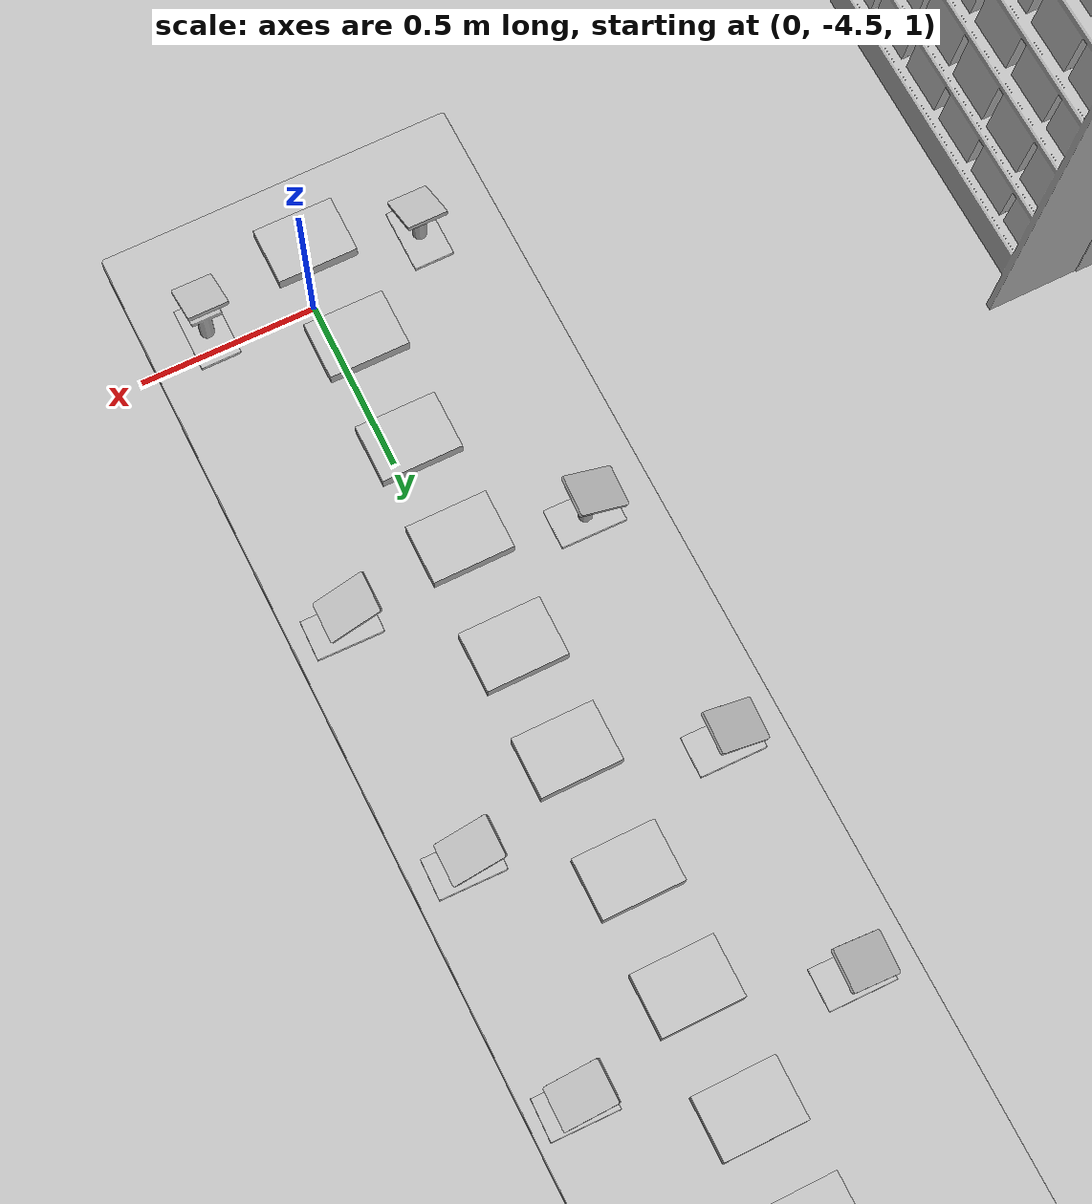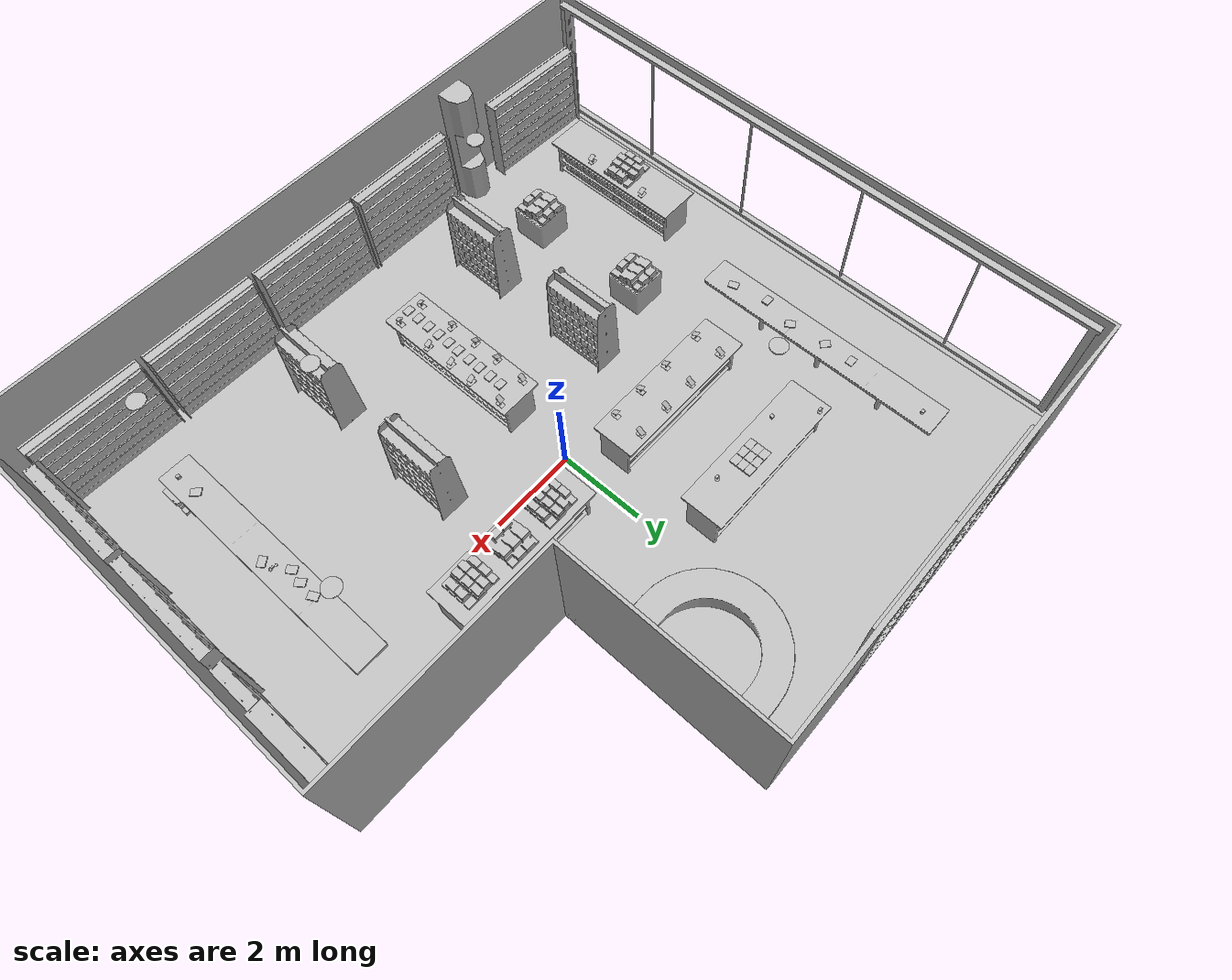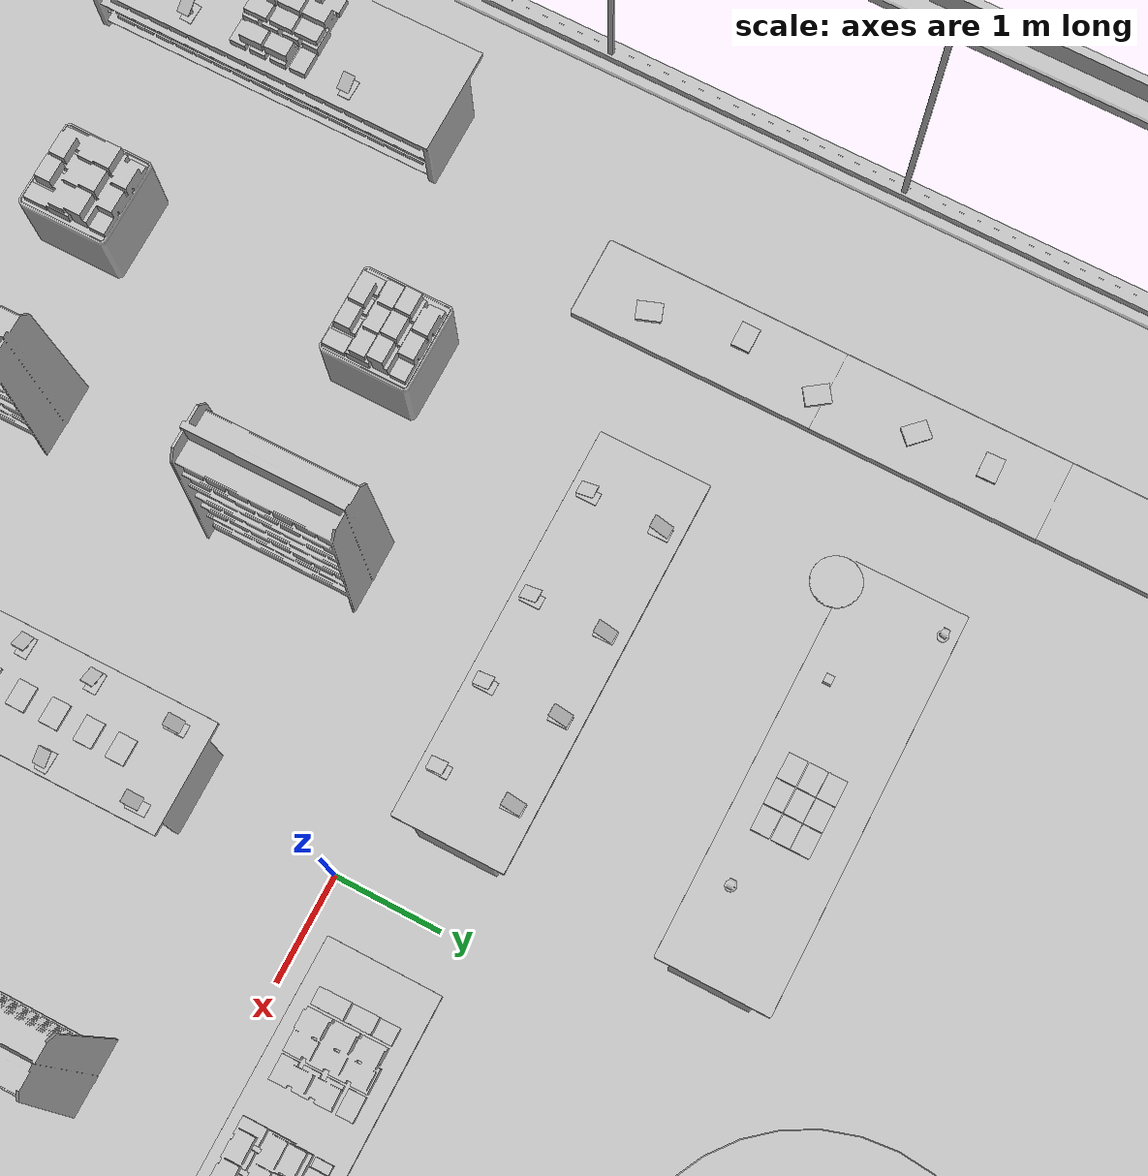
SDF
<sdf version="1.7">
 <world name="default">
  <gravity>0 0 -9.8</gravity>
  <magnetic_field>6e-06 2.3e-05 -4.2e-05</magnetic_field>
  <atmosphere type="adiabatic"/>
  <physics name="default_physics" default="0" type="ode">
   <max_step_size>0.001</max_step_size>
   <real_time_factor>1</real_time_factor>
   <real_time_update_rate>1000</real_time_update_rate>
  </physics>
  <scene>
   <ambient>0.4 0.4 0.4 1</ambient>
   <background>1 1 1 1</background>
   <shadows>1</shadows>
   <grid>0</grid>
   <origin_visual>0</origin_visual>
  </scene>
  <spherical_coordinates>
   <surface_model>EARTH_WGS84</surface_model>
   <latitude_deg>0</latitude_deg>
   <longitude_deg>0</longitude_deg>
   <elevation>0</elevation>
   <heading_deg>0</heading_deg>
  </spherical_coordinates>
  <model name="AirConditionerC_01_001">
   <frame name="aws_robomaker_retail_AirConditionerC_01::__model__" attached_to="aws_robomaker_retail_AirConditionerC_01::link">
    <pose relative_to="__model__">0 0 0 0 -0 0</pose>
   </frame>
   <link name="aws_robomaker_retail_AirConditionerC_01::link">
    <inertial><mass>50</mass></inertial>
    <collision name="collision">
     <geometry>
      <mesh>
       <uri>model://aws_robomaker_retail_AirConditionerC_01/meshes/aws_AirConditionerC_01_collision.DAE</uri>
       <scale>1 1 1</scale>
      </mesh>
     </geometry>
    </collision>
    <visual name="visual">
     <geometry>
      <mesh>
       <uri>model://aws_robomaker_retail_AirConditionerC_01/meshes/aws_AirConditionerC_01_visual.DAE</uri>
      </mesh>
     </geometry>
    </visual>
    <pose relative_to="aws_robomaker_retail_AirConditionerC_01::__model__">0 0 0 0 -0 0</pose>
   </link>
   <static>1</static>
   <pose>7.4582 1.42245 3.29094 0 0 -1.56422</pose>
  </model>
  <model name="Bicycle_01_001">
   <frame name="aws_robomaker_retail_Bicycle_01::__model__" attached_to="aws_robomaker_retail_Bicycle_01::link">
    <pose relative_to="__model__">0 0 0 0 -0 0</pose>
   </frame>
   <link name="aws_robomaker_retail_Bicycle_01::link">
    <inertial>
     <mass>0.04</mass>
     <inertia><ixx>0.1</ixx><ixy>0</ixy><ixz>0</ixz><iyy>0.1</iyy><iyz>0</iyz><izz>0.01</izz></inertia>
    </inertial>
    <collision name="collision">
     <geometry>
      <mesh>
       <uri>model://aws_robomaker_retail_Bicycle_01/meshes/aws_Bicycle_01_collision.DAE</uri>
       <scale>1 1 1</scale>
      </mesh>
     </geometry>
    </collision>
    <visual name="visual">
     <geometry>
      <mesh><uri>model://aws_robomaker_retail_Bicycle_01/meshes/aws_Bicycle_01_visual.DAE</uri></mesh>
     </geometry>
    </visual>
    <pose relative_to="aws_robomaker_retail_Bicycle_01::__model__">0 0 0 0 -0 0</pose>
   </link>
   <static>1</static>
   <pose>5.68125 -2.24245 0.931246 2e-06 -2.4e-05 -0</pose>
  </model>
  <model name="BookE_01_001">
   <frame name="aws_robomaker_retail_BookE_01::__model__" attached_to="aws_robomaker_retail_BookE_01::link">
    <pose relative_to="__model__">0 0 0 0 -0 0</pose>
   </frame>
   <link name="aws_robomaker_retail_BookE_01::link">
    <inertial>
     <mass>1</mass>
     <inertia><ixy>0</ixy><ixz>0</ixz><iyz>0</iyz><ixx>0.0666</ixx><iyy>0.0346</iyy><izz>0.0986</izz></inertia>
    </inertial>
    <collision name="collision">
     <geometry>
      <mesh>
       <uri>model://aws_robomaker_retail_BookE_01/meshes/aws_BookE_01_collision.DAE</uri>
       <scale>1 1 1</scale>
      </mesh>
     </geometry>
    </collision>
    <visual name="visual">
     <geometry>
      <mesh><uri>model://aws_robomaker_retail_BookE_01/meshes/aws_BookE_01_visual.DAE</uri></mesh>
     </geometry>
    </visual>
    <pose relative_to="aws_robomaker_retail_BookE_01::__model__">0 0 0 0 -0 0</pose>
   </link>
   <static>1</static>
   <pose>5.47653 -1.93253 0.948933 4e-06 1e-06 -2.54352</pose>
  </model>
  <model name="BookE_01_002">
   <frame name="aws_robomaker_retail_BookE_01::__model__" attached_to="aws_robomaker_retail_BookE_01::link">
    <pose relative_to="__model__">0 0 0 0 -0 0</pose>
   </frame>
   <link name="aws_robomaker_retail_BookE_01::link">
    <inertial>
     <mass>1</mass>
     <inertia><ixy>0</ixy><ixz>0</ixz><iyz>0</iyz><ixx>0.0666</ixx><iyy>0.0346</iyy><izz>0.0986</izz></inertia>
    </inertial>
    <collision name="collision">
     <geometry>
      <mesh>
       <uri>model://aws_robomaker_retail_BookE_01/meshes/aws_BookE_01_collision.DAE</uri>
       <scale>1 1 1</scale>
      </mesh>
     </geometry>
    </collision>
    <visual name="visual">
     <geometry>
      <mesh><uri>model://aws_robomaker_retail_BookE_01/meshes/aws_BookE_01_visual.DAE</uri></mesh>
     </geometry>
    </visual>
    <pose relative_to="aws_robomaker_retail_BookE_01::__model__">0 0 0 0 -0 0</pose>
   </link>
   <static>1</static>
   <pose>-5.414 3.33067 0.934015 -1e-06 -1e-06 -1.54109</pose>
  </model>
  <model name="BookE_01_003">
   <frame name="aws_robomaker_retail_BookE_01::__model__" attached_to="aws_robomaker_retail_BookE_01::link">
    <pose relative_to="__model__">0 0 0 0 -0 0</pose>
   </frame>
   <link name="aws_robomaker_retail_BookE_01::link">
    <inertial>
     <mass>1</mass>
     <inertia><ixy>0</ixy><ixz>0</ixz><iyz>0</iyz><ixx>0.0666</ixx><iyy>0.0346</iyy><izz>0.0986</izz></inertia>
    </inertial>
    <collision name="collision">
     <geometry>
      <mesh>
       <uri>model://aws_robomaker_retail_BookE_01/meshes/aws_BookE_01_collision.DAE</uri>
       <scale>1 1 1</scale>
      </mesh>
     </geometry>
    </collision>
    <visual name="visual">
     <geometry>
      <mesh><uri>model://aws_robomaker_retail_BookE_01/meshes/aws_BookE_01_visual.DAE</uri></mesh>
     </geometry>
    </visual>
    <pose relative_to="aws_robomaker_retail_BookE_01::__model__">0 0 0 0 -0 0</pose>
   </link>
   <static>1</static>
   <pose>5.55255 -1.21421 0.948933 4e-06 -1e-06 -2.65431</pose>
  </model>
  <model name="BookE_01_004">
   <frame name="aws_robomaker_retail_BookE_01::__model__" attached_to="aws_robomaker_retail_BookE_01::link">
    <pose relative_to="__model__">0 0 0 0 -0 0</pose>
   </frame>
   <link name="aws_robomaker_retail_BookE_01::link">
    <inertial>
     <mass>1</mass>
     <inertia><ixy>0</ixy><ixz>0</ixz><iyz>0</iyz><ixx>0.0666</ixx><iyy>0.0346</iyy><izz>0.0986</izz></inertia>
    </inertial>
    <collision name="collision">
     <geometry>
      <mesh>
       <uri>model://aws_robomaker_retail_BookE_01/meshes/aws_BookE_01_collision.DAE</uri>
       <scale>1 1 1</scale>
      </mesh>
     </geometry>
    </collision>
    <visual name="visual">
     <geometry>
      <mesh><uri>model://aws_robomaker_retail_BookE_01/meshes/aws_BookE_01_visual.DAE</uri></mesh>
     </geometry>
    </visual>
    <pose relative_to="aws_robomaker_retail_BookE_01::__model__">0 0 0 0 -0 0</pose>
   </link>
   <static>1</static>
   <pose>5.67723 -4.6492 0.946394 0.0001 6e-06 -2.35575</pose>
  </model>
  <model name="BookE_01_005">
   <frame name="aws_robomaker_retail_BookE_01::__model__" attached_to="aws_robomaker_retail_BookE_01::link">
    <pose relative_to="__model__">0 0 0 0 -0 0</pose>
   </frame>
   <link name="aws_robomaker_retail_BookE_01::link">
    <inertial>
     <mass>1</mass>
     <inertia><ixy>0</ixy><ixz>0</ixz><iyz>0</iyz><ixx>0.0666</ixx><iyy>0.0346</iyy><izz>0.0986</izz></inertia>
    </inertial>
    <collision name="collision">
     <geometry>
      <mesh>
       <uri>model://aws_robomaker_retail_BookE_01/meshes/aws_BookE_01_collision.DAE</uri>
       <scale>1 1 1</scale>
      </mesh>
     </geometry>
    </collision>
    <visual name="visual">
     <geometry>
      <mesh><uri>model://aws_robomaker_retail_BookE_01/meshes/aws_BookE_01_visual.DAE</uri></mesh>
     </geometry>
    </visual>
    <pose relative_to="aws_robomaker_retail_BookE_01::__model__">0 0 0 0 -0 0</pose>
   </link>
   <static>1</static>
   <pose>5.53815 -1.61032 0.948933 0 0 -2.5269</pose>
  </model>
  <model name="BookE_01_006">
   <frame name="aws_robomaker_retail_BookE_01::__model__" attached_to="aws_robomaker_retail_BookE_01::link">
    <pose relative_to="__model__">0 0 0 0 -0 0</pose>
   </frame>
   <link name="aws_robomaker_retail_BookE_01::link">
    <inertial>
     <mass>1</mass>
     <inertia><ixy>0</ixy><ixz>0</ixz><iyz>0</iyz><ixx>0.0666</ixx><iyy>0.0346</iyy><izz>0.0986</izz></inertia>
    </inertial>
    <collision name="collision">
     <geometry>
      <mesh>
       <uri>model://aws_robomaker_retail_BookE_01/meshes/aws_BookE_01_collision.DAE</uri>
       <scale>1 1 1</scale>
      </mesh>
     </geometry>
    </collision>
    <visual name="visual">
     <geometry>
      <mesh><uri>model://aws_robomaker_retail_BookE_01/meshes/aws_BookE_01_visual.DAE</uri></mesh>
     </geometry>
    </visual>
    <pose relative_to="aws_robomaker_retail_BookE_01::__model__">0 0 0 0 -0 0</pose>
   </link>
   <static>1</static>
   <pose>-1.88942 3.34639 1.05494 0 -0 1.56816</pose>
  </model>
  <model name="BookE_01_007">
   <frame name="aws_robomaker_retail_BookE_01::__model__" attached_to="aws_robomaker_retail_BookE_01::link">
    <pose relative_to="__model__">0 0 0 0 -0 0</pose>
   </frame>
   <link name="aws_robomaker_retail_BookE_01::link">
    <inertial>
     <mass>1</mass>
     <inertia><ixy>0</ixy><ixz>0</ixz><iyz>0</iyz><ixx>0.0666</ixx><iyy>0.0346</iyy><izz>0.0986</izz></inertia>
    </inertial>
    <collision name="collision">
     <geometry>
      <mesh>
       <uri>model://aws_robomaker_retail_BookE_01/meshes/aws_BookE_01_collision.DAE</uri>
       <scale>1 1 1</scale>
      </mesh>
     </geometry>
    </collision>
    <visual name="visual">
     <geometry>
      <mesh><uri>model://aws_robomaker_retail_BookE_01/meshes/aws_BookE_01_visual.DAE</uri></mesh>
     </geometry>
    </visual>
    <pose relative_to="aws_robomaker_retail_BookE_01::__model__">0 0 0 0 -0 0</pose>
   </link>
   <static>1</static>
   <pose>-2.12373 3.34639 1.05494 0 -0 1.56816</pose>
  </model>
  <model name="BookE_01_008">
   <frame name="aws_robomaker_retail_BookE_01::__model__" attached_to="aws_robomaker_retail_BookE_01::link">
    <pose relative_to="__model__">0 0 0 0 -0 0</pose>
   </frame>
   <link name="aws_robomaker_retail_BookE_01::link">
    <inertial>
     <mass>1</mass>
     <inertia><ixy>0</ixy><ixz>0</ixz><iyz>0</iyz><ixx>0.0666</ixx><iyy>0.0346</iyy><izz>0.0986</izz></inertia>
    </inertial>
    <collision name="collision">
     <geometry>
      <mesh>
       <uri>model://aws_robomaker_retail_BookE_01/meshes/aws_BookE_01_collision.DAE</uri>
       <scale>1 1 1</scale>
      </mesh>
     </geometry>
    </collision>
    <visual name="visual">
     <geometry>
      <mesh><uri>model://aws_robomaker_retail_BookE_01/meshes/aws_BookE_01_visual.DAE</uri></mesh>
     </geometry>
    </visual>
    <pose relative_to="aws_robomaker_retail_BookE_01::__model__">0 0 0 0 -0 0</pose>
   </link>
   <static>1</static>
   <pose>-5.31512 1.77195 0.955242 3.14124 -0.072268 -2.52691</pose>
  </model>
  <model name="BookE_01_009">
   <frame name="aws_robomaker_retail_BookE_01::__model__" attached_to="aws_robomaker_retail_BookE_01::link">
    <pose relative_to="__model__">0 0 0 0 -0 0</pose>
   </frame>
   <link name="aws_robomaker_retail_BookE_01::link">
    <inertial>
     <mass>1</mass>
     <inertia><ixy>0</ixy><ixz>0</ixz><iyz>0</iyz><ixx>0.0666</ixx><iyy>0.0346</iyy><izz>0.0986</izz></inertia>
    </inertial>
    <collision name="collision">
     <geometry>
      <mesh>
       <uri>model://aws_robomaker_retail_BookE_01/meshes/aws_BookE_01_collision.DAE</uri>
       <scale>1 1 1</scale>
      </mesh>
     </geometry>
    </collision>
    <visual name="visual">
     <geometry>
      <mesh><uri>model://aws_robomaker_retail_BookE_01/meshes/aws_BookE_01_visual.DAE</uri></mesh>
     </geometry>
    </visual>
    <pose relative_to="aws_robomaker_retail_BookE_01::__model__">0 0 0 0 -0 0</pose>
   </link>
   <static>1</static>
   <pose>1.1702 1.19625 343583 0.002241 -0.0011 -0.623328</pose>
  </model>
  <model name="BookE_01_010">
   <frame name="aws_robomaker_retail_BookE_01::__model__" attached_to="aws_robomaker_retail_BookE_01::link">
    <pose relative_to="__model__">0 0 0 0 -0 0</pose>
   </frame>
   <link name="aws_robomaker_retail_BookE_01::link">
    <inertial>
     <mass>1</mass>
     <inertia><ixy>0</ixy><ixz>0</ixz><iyz>0</iyz><ixx>0.0666</ixx><iyy>0.0346</iyy><izz>0.0986</izz></inertia>
    </inertial>
    <collision name="collision">
     <geometry>
      <mesh>
       <uri>model://aws_robomaker_retail_BookE_01/meshes/aws_BookE_01_collision.DAE</uri>
       <scale>1 1 1</scale>
      </mesh>
     </geometry>
    </collision>
    <visual name="visual">
     <geometry>
      <mesh><uri>model://aws_robomaker_retail_BookE_01/meshes/aws_BookE_01_visual.DAE</uri></mesh>
     </geometry>
    </visual>
    <pose relative_to="aws_robomaker_retail_BookE_01::__model__">0 0 0 0 -0 0</pose>
   </link>
   <static>1</static>
   <pose>-5.50342 1.01206 0.941463 0 0 -1.56844</pose>
  </model>
  <model name="BookE_01_011">
   <frame name="aws_robomaker_retail_BookE_01::__model__" attached_to="aws_robomaker_retail_BookE_01::link">
    <pose relative_to="__model__">0 0 0 0 -0 0</pose>
   </frame>
   <link name="aws_robomaker_retail_BookE_01::link">
    <inertial>
     <mass>1</mass>
     <inertia><ixy>0</ixy><ixz>0</ixz><iyz>0</iyz><ixx>0.0666</ixx><iyy>0.0346</iyy><izz>0.0986</izz></inertia>
    </inertial>
    <collision name="collision">
     <geometry>
      <mesh>
       <uri>model://aws_robomaker_retail_BookE_01/meshes/aws_BookE_01_collision.DAE</uri>
       <scale>1 1 1</scale>
      </mesh>
     </geometry>
    </collision>
    <visual name="visual">
     <geometry>
      <mesh><uri>model://aws_robomaker_retail_BookE_01/meshes/aws_BookE_01_visual.DAE</uri></mesh>
     </geometry>
    </visual>
    <pose relative_to="aws_robomaker_retail_BookE_01::__model__">0 0 0 0 -0 0</pose>
   </link>
   <static>1</static>
   <pose>5.74923 -2.49202 0.948933 2e-06 1e-06 2.22339</pose>
  </model>
  <model name="BookE_01_012">
   <frame name="aws_robomaker_retail_BookE_01::__model__" attached_to="aws_robomaker_retail_BookE_01::link">
    <pose relative_to="__model__">0 0 0 0 -0 0</pose>
   </frame>
   <link name="aws_robomaker_retail_BookE_01::link">
    <inertial>
     <mass>1</mass>
     <inertia><ixy>0</ixy><ixz>0</ixz><iyz>0</iyz><ixx>0.0666</ixx><iyy>0.0346</iyy><izz>0.0986</izz></inertia>
    </inertial>
    <collision name="collision">
     <geometry>
      <mesh>
       <uri>model://aws_robomaker_retail_BookE_01/meshes/aws_BookE_01_collision.DAE</uri>
       <scale>1 1 1</scale>
      </mesh>
     </geometry>
    </collision>
    <visual name="visual">
     <geometry>
      <mesh><uri>model://aws_robomaker_retail_BookE_01/meshes/aws_BookE_01_visual.DAE</uri></mesh>
     </geometry>
    </visual>
    <pose relative_to="aws_robomaker_retail_BookE_01::__model__">0 0 0 0 -0 0</pose>
   </link>
   <static>1</static>
   <pose>-5.33358 0.186186 0.949316 -1e-06 -0.004549 -2.79848</pose>
  </model>
  <model name="BookE_01_013">
   <frame name="aws_robomaker_retail_BookE_01::__model__" attached_to="aws_robomaker_retail_BookE_01::link">
    <pose relative_to="__model__">0 0 0 0 -0 0</pose>
   </frame>
   <link name="aws_robomaker_retail_BookE_01::link">
    <inertial>
     <mass>1</mass>
     <inertia><ixy>0</ixy><ixz>0</ixz><iyz>0</iyz><ixx>0.0666</ixx><iyy>0.0346</iyy><izz>0.0986</izz></inertia>
    </inertial>
    <collision name="collision">
     <geometry>
      <mesh>
       <uri>model://aws_robomaker_retail_BookE_01/meshes/aws_BookE_01_collision.DAE</uri>
       <scale>1 1 1</scale>
      </mesh>
     </geometry>
    </collision>
    <visual name="visual">
     <geometry>
      <mesh><uri>model://aws_robomaker_retail_BookE_01/meshes/aws_BookE_01_visual.DAE</uri></mesh>
     </geometry>
    </visual>
    <pose relative_to="aws_robomaker_retail_BookE_01::__model__">0 0 0 0 -0 0</pose>
   </link>
   <static>1</static>
   <pose>-5.40391 2.65088 0.931119 0.021204 -1e-06 -2.35575</pose>
  </model>
  <model name="BookE_01_014">
   <frame name="aws_robomaker_retail_BookE_01::__model__" attached_to="aws_robomaker_retail_BookE_01::link">
    <pose relative_to="__model__">0 0 0 0 -0 0</pose>
   </frame>
   <link name="aws_robomaker_retail_BookE_01::link">
    <inertial>
     <mass>1</mass>
     <inertia><ixy>0</ixy><ixz>0</ixz><iyz>0</iyz><ixx>0.0666</ixx><iyy>0.0346</iyy><izz>0.0986</izz></inertia>
    </inertial>
    <collision name="collision">
     <geometry>
      <mesh>
       <uri>model://aws_robomaker_retail_BookE_01/meshes/aws_BookE_01_collision.DAE</uri>
       <scale>1 1 1</scale>
      </mesh>
     </geometry>
    </collision>
    <visual name="visual">
     <geometry>
      <mesh><uri>model://aws_robomaker_retail_BookE_01/meshes/aws_BookE_01_visual.DAE</uri></mesh>
     </geometry>
    </visual>
    <pose relative_to="aws_robomaker_retail_BookE_01::__model__">0 0 0 0 -0 0</pose>
   </link>
   <static>1</static>
   <pose>-1.88942 2.99369 1.05494 0 -0 1.56816</pose>
  </model>
  <model name="BookE_01_015">
   <frame name="aws_robomaker_retail_BookE_01::__model__" attached_to="aws_robomaker_retail_BookE_01::link">
    <pose relative_to="__model__">0 0 0 0 -0 0</pose>
   </frame>
   <link name="aws_robomaker_retail_BookE_01::link">
    <inertial>
     <mass>1</mass>
     <inertia><ixy>0</ixy><ixz>0</ixz><iyz>0</iyz><ixx>0.0666</ixx><iyy>0.0346</iyy><izz>0.0986</izz></inertia>
    </inertial>
    <collision name="collision">
     <geometry>
      <mesh>
       <uri>model://aws_robomaker_retail_BookE_01/meshes/aws_BookE_01_collision.DAE</uri>
       <scale>1 1 1</scale>
      </mesh>
     </geometry>
    </collision>
    <visual name="visual">
     <geometry>
      <mesh><uri>model://aws_robomaker_retail_BookE_01/meshes/aws_BookE_01_visual.DAE</uri></mesh>
     </geometry>
    </visual>
    <pose relative_to="aws_robomaker_retail_BookE_01::__model__">0 0 0 0 -0 0</pose>
   </link>
   <static>1</static>
   <pose>-2.12373 2.99369 1.05494 0 -0 1.56816</pose>
  </model>
  <model name="BookE_01_016">
   <frame name="aws_robomaker_retail_BookE_01::__model__" attached_to="aws_robomaker_retail_BookE_01::link">
    <pose relative_to="__model__">0 0 0 0 -0 0</pose>
   </frame>
   <link name="aws_robomaker_retail_BookE_01::link">
    <inertial>
     <mass>1</mass>
     <inertia><ixy>0</ixy><ixz>0</ixz><iyz>0</iyz><ixx>0.0666</ixx><iyy>0.0346</iyy><izz>0.0986</izz></inertia>
    </inertial>
    <collision name="collision">
     <geometry>
      <mesh>
       <uri>model://aws_robomaker_retail_BookE_01/meshes/aws_BookE_01_collision.DAE</uri>
       <scale>1 1 1</scale>
      </mesh>
     </geometry>
    </collision>
    <visual name="visual">
     <geometry>
      <mesh><uri>model://aws_robomaker_retail_BookE_01/meshes/aws_BookE_01_visual.DAE</uri></mesh>
     </geometry>
    </visual>
    <pose relative_to="aws_robomaker_retail_BookE_01::__model__">0 0 0 0 -0 0</pose>
   </link>
   <static>1</static>
   <pose>-2.35737 2.99369 1.05494 0 -0 1.56816</pose>
  </model>
  <model name="BookE_01_017">
   <frame name="aws_robomaker_retail_BookE_01::__model__" attached_to="aws_robomaker_retail_BookE_01::link">
    <pose relative_to="__model__">0 0 0 0 -0 0</pose>
   </frame>
   <link name="aws_robomaker_retail_BookE_01::link">
    <inertial>
     <mass>1</mass>
     <inertia><ixy>0</ixy><ixz>0</ixz><iyz>0</iyz><ixx>0.0666</ixx><iyy>0.0346</iyy><izz>0.0986</izz></inertia>
    </inertial>
    <collision name="collision">
     <geometry>
      <mesh>
       <uri>model://aws_robomaker_retail_BookE_01/meshes/aws_BookE_01_collision.DAE</uri>
       <scale>1 1 1</scale>
      </mesh>
     </geometry>
    </collision>
    <visual name="visual">
     <geometry>
      <mesh><uri>model://aws_robomaker_retail_BookE_01/meshes/aws_BookE_01_visual.DAE</uri></mesh>
     </geometry>
    </visual>
    <pose relative_to="aws_robomaker_retail_BookE_01::__model__">0 0 0 0 -0 0</pose>
   </link>
   <static>1</static>
   <pose>-1.88942 3.17292 1.05494 0 -0 1.56816</pose>
  </model>
  <model name="BookE_01_018">
   <frame name="aws_robomaker_retail_BookE_01::__model__" attached_to="aws_robomaker_retail_BookE_01::link">
    <pose relative_to="__model__">0 0 0 0 -0 0</pose>
   </frame>
   <link name="aws_robomaker_retail_BookE_01::link">
    <inertial>
     <mass>1</mass>
     <inertia><ixy>0</ixy><ixz>0</ixz><iyz>0</iyz><ixx>0.0666</ixx><iyy>0.0346</iyy><izz>0.0986</izz></inertia>
    </inertial>
    <collision name="collision">
     <geometry>
      <mesh>
       <uri>model://aws_robomaker_retail_BookE_01/meshes/aws_BookE_01_collision.DAE</uri>
       <scale>1 1 1</scale>
      </mesh>
     </geometry>
    </collision>
    <visual name="visual">
     <geometry>
      <mesh><uri>model://aws_robomaker_retail_BookE_01/meshes/aws_BookE_01_visual.DAE</uri></mesh>
     </geometry>
    </visual>
    <pose relative_to="aws_robomaker_retail_BookE_01::__model__">0 0 0 0 -0 0</pose>
   </link>
   <static>1</static>
   <pose>-2.12373 3.17292 1.05494 0 -0 1.56816</pose>
  </model>
  <model name="BookE_01_019">
   <frame name="aws_robomaker_retail_BookE_01::__model__" attached_to="aws_robomaker_retail_BookE_01::link">
    <pose relative_to="__model__">0 0 0 0 -0 0</pose>
   </frame>
   <link name="aws_robomaker_retail_BookE_01::link">
    <inertial>
     <mass>1</mass>
     <inertia><ixy>0</ixy><ixz>0</ixz><iyz>0</iyz><ixx>0.0666</ixx><iyy>0.0346</iyy><izz>0.0986</izz></inertia>
    </inertial>
    <collision name="collision">
     <geometry>
      <mesh>
       <uri>model://aws_robomaker_retail_BookE_01/meshes/aws_BookE_01_collision.DAE</uri>
       <scale>1 1 1</scale>
      </mesh>
     </geometry>
    </collision>
    <visual name="visual">
     <geometry>
      <mesh><uri>model://aws_robomaker_retail_BookE_01/meshes/aws_BookE_01_visual.DAE</uri></mesh>
     </geometry>
    </visual>
    <pose relative_to="aws_robomaker_retail_BookE_01::__model__">0 0 0 0 -0 0</pose>
   </link>
   <static>1</static>
   <pose>-2.35737 3.17292 1.05494 0 -0 1.56816</pose>
  </model>
  <model name="BookE_01_020">
   <frame name="aws_robomaker_retail_BookE_01::__model__" attached_to="aws_robomaker_retail_BookE_01::link">
    <pose relative_to="__model__">0 0 0 0 -0 0</pose>
   </frame>
   <link name="aws_robomaker_retail_BookE_01::link">
    <inertial>
     <mass>1</mass>
     <inertia><ixy>0</ixy><ixz>0</ixz><iyz>0</iyz><ixx>0.0666</ixx><iyy>0.0346</iyy><izz>0.0986</izz></inertia>
    </inertial>
    <collision name="collision">
     <geometry>
      <mesh>
       <uri>model://aws_robomaker_retail_BookE_01/meshes/aws_BookE_01_collision.DAE</uri>
       <scale>1 1 1</scale>
      </mesh>
     </geometry>
    </collision>
    <visual name="visual">
     <geometry>
      <mesh><uri>model://aws_robomaker_retail_BookE_01/meshes/aws_BookE_01_visual.DAE</uri></mesh>
     </geometry>
    </visual>
    <pose relative_to="aws_robomaker_retail_BookE_01::__model__">0 0 0 0 -0 0</pose>
   </link>
   <static>1</static>
   <pose>-0.040981 -2.44797 1.05383 4e-06 -4e-06 -1.57338</pose>
  </model>
  <model name="BookE_01_021">
   <frame name="aws_robomaker_retail_BookE_01::__model__" attached_to="aws_robomaker_retail_BookE_01::link">
    <pose relative_to="__model__">0 0 0 0 -0 0</pose>
   </frame>
   <link name="aws_robomaker_retail_BookE_01::link">
    <inertial>
     <mass>1</mass>
     <inertia><ixy>0</ixy><ixz>0</ixz><iyz>0</iyz><ixx>0.0666</ixx><iyy>0.0346</iyy><izz>0.0986</izz></inertia>
    </inertial>
    <collision name="collision">
     <geometry>
      <mesh>
       <uri>model://aws_robomaker_retail_BookE_01/meshes/aws_BookE_01_collision.DAE</uri>
       <scale>1 1 1</scale>
      </mesh>
     </geometry>
    </collision>
    <visual name="visual">
     <geometry>
      <mesh><uri>model://aws_robomaker_retail_BookE_01/meshes/aws_BookE_01_visual.DAE</uri></mesh>
     </geometry>
    </visual>
    <pose relative_to="aws_robomaker_retail_BookE_01::__model__">0 0 0 0 -0 0</pose>
   </link>
   <static>1</static>
   <pose>-0.044005 -2.76115 1.05383 4e-06 -4e-06 -1.57338</pose>
  </model>
  <model name="BookE_01_022">
   <frame name="aws_robomaker_retail_BookE_01::__model__" attached_to="aws_robomaker_retail_BookE_01::link">
    <pose relative_to="__model__">0 0 0 0 -0 0</pose>
   </frame>
   <link name="aws_robomaker_retail_BookE_01::link">
    <inertial>
     <mass>1</mass>
     <inertia><ixy>0</ixy><ixz>0</ixz><iyz>0</iyz><ixx>0.0666</ixx><iyy>0.0346</iyy><izz>0.0986</izz></inertia>
    </inertial>
    <collision name="collision">
     <geometry>
      <mesh>
       <uri>model://aws_robomaker_retail_BookE_01/meshes/aws_BookE_01_collision.DAE</uri>
       <scale>1 1 1</scale>
      </mesh>
     </geometry>
    </collision>
    <visual name="visual">
     <geometry>
      <mesh><uri>model://aws_robomaker_retail_BookE_01/meshes/aws_BookE_01_visual.DAE</uri></mesh>
     </geometry>
    </visual>
    <pose relative_to="aws_robomaker_retail_BookE_01::__model__">0 0 0 0 -0 0</pose>
   </link>
   <static>1</static>
   <pose>-0.046637 -3.09718 1.05383 4e-06 -4e-06 -1.57338</pose>
  </model>
  <model name="BookE_01_023">
   <frame name="aws_robomaker_retail_BookE_01::__model__" attached_to="aws_robomaker_retail_BookE_01::link">
    <pose relative_to="__model__">0 0 0 0 -0 0</pose>
   </frame>
   <link name="aws_robomaker_retail_BookE_01::link">
    <inertial>
     <mass>1</mass>
     <inertia><ixy>0</ixy><ixz>0</ixz><iyz>0</iyz><ixx>0.0666</ixx><iyy>0.0346</iyy><izz>0.0986</izz></inertia>
    </inertial>
    <collision name="collision">
     <geometry>
      <mesh>
       <uri>model://aws_robomaker_retail_BookE_01/meshes/aws_BookE_01_collision.DAE</uri>
       <scale>1 1 1</scale>
      </mesh>
     </geometry>
    </collision>
    <visual name="visual">
     <geometry>
      <mesh><uri>model://aws_robomaker_retail_BookE_01/meshes/aws_BookE_01_visual.DAE</uri></mesh>
     </geometry>
    </visual>
    <pose relative_to="aws_robomaker_retail_BookE_01::__model__">0 0 0 0 -0 0</pose>
   </link>
   <static>1</static>
   <pose>-0.049416 -3.40021 1.05383 4e-06 -4e-06 -1.57338</pose>
  </model>
  <model name="BookE_01_024">
   <frame name="aws_robomaker_retail_BookE_01::__model__" attached_to="aws_robomaker_retail_BookE_01::link">
    <pose relative_to="__model__">0 0 0 0 -0 0</pose>
   </frame>
   <link name="aws_robomaker_retail_BookE_01::link">
    <inertial>
     <mass>1</mass>
     <inertia><ixy>0</ixy><ixz>0</ixz><iyz>0</iyz><ixx>0.0666</ixx><iyy>0.0346</iyy><izz>0.0986</izz></inertia>
    </inertial>
    <collision name="collision">
     <geometry>
      <mesh>
       <uri>model://aws_robomaker_retail_BookE_01/meshes/aws_BookE_01_collision.DAE</uri>
       <scale>1 1 1</scale>
      </mesh>
     </geometry>
    </collision>
    <visual name="visual">
     <geometry>
      <mesh><uri>model://aws_robomaker_retail_BookE_01/meshes/aws_BookE_01_visual.DAE</uri></mesh>
     </geometry>
    </visual>
    <pose relative_to="aws_robomaker_retail_BookE_01::__model__">0 0 0 0 -0 0</pose>
   </link>
   <static>1</static>
   <pose>-0.054192 -3.71798 1.05383 4e-06 -4e-06 -1.57338</pose>
  </model>
  <model name="BookE_01_025">
   <frame name="aws_robomaker_retail_BookE_01::__model__" attached_to="aws_robomaker_retail_BookE_01::link">
    <pose relative_to="__model__">0 0 0 0 -0 0</pose>
   </frame>
   <link name="aws_robomaker_retail_BookE_01::link">
    <inertial>
     <mass>1</mass>
     <inertia><ixy>0</ixy><ixz>0</ixz><iyz>0</iyz><ixx>0.0666</ixx><iyy>0.0346</iyy><izz>0.0986</izz></inertia>
    </inertial>
    <collision name="collision">
     <geometry>
      <mesh>
       <uri>model://aws_robomaker_retail_BookE_01/meshes/aws_BookE_01_collision.DAE</uri>
       <scale>1 1 1</scale>
      </mesh>
     </geometry>
    </collision>
    <visual name="visual">
     <geometry>
      <mesh><uri>model://aws_robomaker_retail_BookE_01/meshes/aws_BookE_01_visual.DAE</uri></mesh>
     </geometry>
    </visual>
    <pose relative_to="aws_robomaker_retail_BookE_01::__model__">0 0 0 0 -0 0</pose>
   </link>
   <static>1</static>
   <pose>-0.056891 -4.02587 1.05383 4e-06 -4e-06 -1.57338</pose>
  </model>
  <model name="BookE_01_026">
   <frame name="aws_robomaker_retail_BookE_01::__model__" attached_to="aws_robomaker_retail_BookE_01::link">
    <pose relative_to="__model__">0 0 0 0 -0 0</pose>
   </frame>
   <link name="aws_robomaker_retail_BookE_01::link">
    <inertial>
     <mass>1</mass>
     <inertia><ixy>0</ixy><ixz>0</ixz><iyz>0</iyz><ixx>0.0666</ixx><iyy>0.0346</iyy><izz>0.0986</izz></inertia>
    </inertial>
    <collision name="collision">
     <geometry>
      <mesh>
       <uri>model://aws_robomaker_retail_BookE_01/meshes/aws_BookE_01_collision.DAE</uri>
       <scale>1 1 1</scale>
      </mesh>
     </geometry>
    </collision>
    <visual name="visual">
     <geometry>
      <mesh><uri>model://aws_robomaker_retail_BookE_01/meshes/aws_BookE_01_visual.DAE</uri></mesh>
     </geometry>
    </visual>
    <pose relative_to="aws_robomaker_retail_BookE_01::__model__">0 0 0 0 -0 0</pose>
   </link>
   <static>1</static>
   <pose>-0.059434 -4.35128 1.05383 4e-06 -4e-06 -1.57338</pose>
  </model>
  <model name="BookE_01_027">
   <frame name="aws_robomaker_retail_BookE_01::__model__" attached_to="aws_robomaker_retail_BookE_01::link">
    <pose relative_to="__model__">0 0 0 0 -0 0</pose>
   </frame>
   <link name="aws_robomaker_retail_BookE_01::link">
    <inertial>
     <mass>1</mass>
     <inertia><ixy>0</ixy><ixz>0</ixz><iyz>0</iyz><ixx>0.0666</ixx><iyy>0.0346</iyy><izz>0.0986</izz></inertia>
    </inertial>
    <collision name="collision">
     <geometry>
      <mesh>
       <uri>model://aws_robomaker_retail_BookE_01/meshes/aws_BookE_01_collision.DAE</uri>
       <scale>1 1 1</scale>
      </mesh>
     </geometry>
    </collision>
    <visual name="visual">
     <geometry>
      <mesh><uri>model://aws_robomaker_retail_BookE_01/meshes/aws_BookE_01_visual.DAE</uri></mesh>
     </geometry>
    </visual>
    <pose relative_to="aws_robomaker_retail_BookE_01::__model__">0 0 0 0 -0 0</pose>
   </link>
   <static>1</static>
   <pose>-0.05398 -4.66203 1.05383 4e-06 -4e-06 -1.57338</pose>
  </model>
  <model name="BookE_01_028">
   <frame name="aws_robomaker_retail_BookE_01::__model__" attached_to="aws_robomaker_retail_BookE_01::link">
    <pose relative_to="__model__">0 0 0 0 -0 0</pose>
   </frame>
   <link name="aws_robomaker_retail_BookE_01::link">
    <inertial>
     <mass>1</mass>
     <inertia><ixy>0</ixy><ixz>0</ixz><iyz>0</iyz><ixx>0.0666</ixx><iyy>0.0346</iyy><izz>0.0986</izz></inertia>
    </inertial>
    <collision name="collision">
     <geometry>
      <mesh>
       <uri>model://aws_robomaker_retail_BookE_01/meshes/aws_BookE_01_collision.DAE</uri>
       <scale>1 1 1</scale>
      </mesh>
     </geometry>
    </collision>
    <visual name="visual">
     <geometry>
      <mesh><uri>model://aws_robomaker_retail_BookE_01/meshes/aws_BookE_01_visual.DAE</uri></mesh>
     </geometry>
    </visual>
    <pose relative_to="aws_robomaker_retail_BookE_01::__model__">0 0 0 0 -0 0</pose>
   </link>
   <static>1</static>
   <pose>-0.037898 -2.12862 1.05383 4e-06 -4e-06 -1.57338</pose>
  </model>
  <model name="BookE_01_029">
   <frame name="aws_robomaker_retail_BookE_01::__model__" attached_to="aws_robomaker_retail_BookE_01::link">
    <pose relative_to="__model__">0 0 0 0 -0 0</pose>
   </frame>
   <link name="aws_robomaker_retail_BookE_01::link">
    <inertial>
     <mass>1</mass>
     <inertia><ixy>0</ixy><ixz>0</ixz><iyz>0</iyz><ixx>0.0666</ixx><iyy>0.0346</iyy><izz>0.0986</izz></inertia>
    </inertial>
    <collision name="collision">
     <geometry>
      <mesh>
       <uri>model://aws_robomaker_retail_BookE_01/meshes/aws_BookE_01_collision.DAE</uri>
       <scale>1 1 1</scale>
      </mesh>
     </geometry>
    </collision>
    <visual name="visual">
     <geometry>
      <mesh><uri>model://aws_robomaker_retail_BookE_01/meshes/aws_BookE_01_visual.DAE</uri></mesh>
     </geometry>
    </visual>
    <pose relative_to="aws_robomaker_retail_BookE_01::__model__">0 0 0 0 -0 0</pose>
   </link>
   <static>1</static>
   <pose>-0.037926 -1.83039 1.05383 4e-06 -4e-06 -1.57338</pose>
  </model>
  <model name="BookE_01_030">
   <frame name="aws_robomaker_retail_BookE_01::__model__" attached_to="aws_robomaker_retail_BookE_01::link">
    <pose relative_to="__model__">0 0 0 0 -0 0</pose>
   </frame>
   <link name="aws_robomaker_retail_BookE_01::link">
    <inertial>
     <mass>1</mass>
     <inertia><ixy>0</ixy><ixz>0</ixz><iyz>0</iyz><ixx>0.0666</ixx><iyy>0.0346</iyy><izz>0.0986</izz></inertia>
    </inertial>
    <collision name="collision">
     <geometry>
      <mesh>
       <uri>model://aws_robomaker_retail_BookE_01/meshes/aws_BookE_01_collision.DAE</uri>
       <scale>1 1 1</scale>
      </mesh>
     </geometry>
    </collision>
    <visual name="visual">
     <geometry>
      <mesh><uri>model://aws_robomaker_retail_BookE_01/meshes/aws_BookE_01_visual.DAE</uri></mesh>
     </geometry>
    </visual>
    <pose relative_to="aws_robomaker_retail_BookE_01::__model__">0 0 0 0 -0 0</pose>
   </link>
   <static>1</static>
   <pose>-2.35737 3.34639 1.05494 0 -0 1.56816</pose>
  </model>
  <model name="BookD_01_001">
   <frame name="aws_robomaker_retail_BookD_01::__model__" attached_to="aws_robomaker_retail_BookD_01::link">
    <pose relative_to="__model__">0 0 0 0 -0 0</pose>
   </frame>
   <link name="aws_robomaker_retail_BookD_01::link">
    <inertial><mass>0.5</mass></inertial>
    <collision name="collision">
     <geometry>
      <mesh>
       <uri>model://aws_robomaker_retail_BookD_01/meshes/aws_BookD_01_collision.DAE</uri>
       <scale>1 1 1</scale>
      </mesh>
     </geometry>
    </collision>
    <visual name="visual">
     <geometry>
      <mesh><uri>model://aws_robomaker_retail_BookD_01/meshes/aws_BookD_01_visual.DAE</uri></mesh>
     </geometry>
    </visual>
    <pose relative_to="aws_robomaker_retail_BookD_01::__model__">0 0 0 0 -0 0</pose>
   </link>
   <static>1</static>
   <pose>5.72005 -5.36588 0.022179 0.003452 -1e-06 0.000652</pose>
  </model>
  <model name="BookD_01_002">
   <frame name="aws_robomaker_retail_BookD_01::__model__" attached_to="aws_robomaker_retail_BookD_01::link">
    <pose relative_to="__model__">0 0 0 0 -0 0</pose>
   </frame>
   <link name="aws_robomaker_retail_BookD_01::link">
    <inertial><mass>0.5</mass></inertial>
    <collision name="collision">
     <geometry>
      <mesh>
       <uri>model://aws_robomaker_retail_BookD_01/meshes/aws_BookD_01_collision.DAE</uri>
       <scale>1 1 1</scale>
      </mesh>
     </geometry>
    </collision>
    <visual name="visual">
     <geometry>
      <mesh><uri>model://aws_robomaker_retail_BookD_01/meshes/aws_BookD_01_visual.DAE</uri></mesh>
     </geometry>
    </visual>
    <pose relative_to="aws_robomaker_retail_BookD_01::__model__">0 0 0 0 -0 0</pose>
   </link>
   <static>1</static>
   <pose>-4.20712 -1.75721 0.804482 0 0 -4e-06</pose>
  </model>
  <model name="BookF_01_003">
   <frame name="aws_robomaker_retail_BookF_01::__model__" attached_to="aws_robomaker_retail_BookF_01::link">
    <pose relative_to="__model__">0 0 0 0 -0 0</pose>
   </frame>
   <link name="aws_robomaker_retail_BookF_01::link">
    <inertial>
     <mass>10</mass>
     <inertia>
      <ixx>0.583817</ixx>
      <ixy>0</ixy>
      <ixz>0</ixz>
      <iyy>0.502925</iyy>
      <iyz>0</iyz>
      <izz>0.99304</izz>
     </inertia>
    </inertial>
    <collision name="collision">
     <geometry>
      <mesh>
       <uri>model://aws_robomaker_retail_BookF_01/meshes/aws_BookF_01_collision.DAE</uri>
       <scale>1 1 1</scale>
      </mesh>
     </geometry>
    </collision>
    <visual name="visual">
     <geometry>
      <mesh><uri>model://aws_robomaker_retail_BookF_01/meshes/aws_BookF_01_visual.DAE</uri></mesh>
     </geometry>
    </visual>
    <pose relative_to="aws_robomaker_retail_BookF_01::__model__">0 0 0 0 -0 0</pose>
   </link>
   <static>1</static>
   <pose>-4.19124 -4.6828 0.804483 4e-06 -0 0</pose>
  </model>
  <model name="BookD_01_003">
   <frame name="aws_robomaker_retail_BookD_01::__model__" attached_to="aws_robomaker_retail_BookD_01::link">
    <pose relative_to="__model__">0 0 0 0 -0 0</pose>
   </frame>
   <link name="aws_robomaker_retail_BookD_01::link">
    <inertial><mass>0.5</mass></inertial>
    <collision name="collision">
     <geometry>
      <mesh>
       <uri>model://aws_robomaker_retail_BookD_01/meshes/aws_BookD_01_collision.DAE</uri>
       <scale>1 1 1</scale>
      </mesh>
     </geometry>
    </collision>
    <visual name="visual">
     <geometry>
      <mesh><uri>model://aws_robomaker_retail_BookD_01/meshes/aws_BookD_01_visual.DAE</uri></mesh>
     </geometry>
    </visual>
    <pose relative_to="aws_robomaker_retail_BookD_01::__model__">0 0 0 0 -0 0</pose>
   </link>
   <static>1</static>
   <pose>-6.23561 -3.78518 1.03816 8e-06 -0 1.58038</pose>
  </model>
  <model name="BookF_01_004">
   <frame name="aws_robomaker_retail_BookF_01::__model__" attached_to="aws_robomaker_retail_BookF_01::link">
    <pose relative_to="__model__">0 0 0 0 -0 0</pose>
   </frame>
   <link name="aws_robomaker_retail_BookF_01::link">
    <inertial>
     <mass>10</mass>
     <inertia>
      <ixx>0.583817</ixx>
      <ixy>0</ixy>
      <ixz>0</ixz>
      <iyy>0.502925</iyy>
      <iyz>0</iyz>
      <izz>0.99304</izz>
     </inertia>
    </inertial>
    <collision name="collision">
     <geometry>
      <mesh>
       <uri>model://aws_robomaker_retail_BookF_01/meshes/aws_BookF_01_collision.DAE</uri>
       <scale>1 1 1</scale>
      </mesh>
     </geometry>
    </collision>
    <visual name="visual">
     <geometry>
      <mesh><uri>model://aws_robomaker_retail_BookF_01/meshes/aws_BookF_01_visual.DAE</uri></mesh>
     </geometry>
    </visual>
    <pose relative_to="aws_robomaker_retail_BookF_01::__model__">0 0 0 0 -0 0</pose>
   </link>
   <static>1</static>
   <pose>1.26164 0.856469 1.03816 8e-06 -0 1.58038</pose>
  </model>
  <model name="BookD_01_004">
   <frame name="aws_robomaker_retail_BookD_01::__model__" attached_to="aws_robomaker_retail_BookD_01::link">
    <pose relative_to="__model__">0 0 0 0 -0 0</pose>
   </frame>
   <link name="aws_robomaker_retail_BookD_01::link">
    <inertial><mass>0.5</mass></inertial>
    <collision name="collision">
     <geometry>
      <mesh>
       <uri>model://aws_robomaker_retail_BookD_01/meshes/aws_BookD_01_collision.DAE</uri>
       <scale>1 1 1</scale>
      </mesh>
     </geometry>
    </collision>
    <visual name="visual">
     <geometry>
      <mesh><uri>model://aws_robomaker_retail_BookD_01/meshes/aws_BookD_01_visual.DAE</uri></mesh>
     </geometry>
    </visual>
    <pose relative_to="aws_robomaker_retail_BookD_01::__model__">0 0 0 0 -0 0</pose>
   </link>
   <static>1</static>
   <pose>2.35863 0.854853 1.03815 6e-06 -0 0.001712</pose>
  </model>
  <model name="BookF_01_005">
   <frame name="aws_robomaker_retail_BookF_01::__model__" attached_to="aws_robomaker_retail_BookF_01::link">
    <pose relative_to="__model__">0 0 0 0 -0 0</pose>
   </frame>
   <link name="aws_robomaker_retail_BookF_01::link">
    <inertial>
     <mass>10</mass>
     <inertia>
      <ixx>0.583817</ixx>
      <ixy>0</ixy>
      <ixz>0</ixz>
      <iyy>0.502925</iyy>
      <iyz>0</iyz>
      <izz>0.99304</izz>
     </inertia>
    </inertial>
    <collision name="collision">
     <geometry>
      <mesh>
       <uri>model://aws_robomaker_retail_BookF_01/meshes/aws_BookF_01_collision.DAE</uri>
       <scale>1 1 1</scale>
      </mesh>
     </geometry>
    </collision>
    <visual name="visual">
     <geometry>
      <mesh><uri>model://aws_robomaker_retail_BookF_01/meshes/aws_BookF_01_visual.DAE</uri></mesh>
     </geometry>
    </visual>
    <pose relative_to="aws_robomaker_retail_BookF_01::__model__">0 0 0 0 -0 0</pose>
   </link>
   <static>1</static>
   <pose>3.43061 0.856469 1.03816 8e-06 -0 1.58038</pose>
  </model>
  <model name="BookshelfA_01_001">
   <frame name="aws_robomaker_retail_BookshelfA_01::__model__" attached_to="aws_robomaker_retail_BookshelfA_01::link">
    <pose relative_to="__model__">0 0 0 0 -0 0</pose>
   </frame>
   <link name="aws_robomaker_retail_BookshelfA_01::link">
    <inertial>
     <mass>50</mass>
     <inertia><ixx>27.7341</ixx><ixy>0</ixy><ixz>0</ixz><iyy>20.9361</iyy><iyz>0</iyz><izz>11.3596</izz></inertia>
    </inertial>
    <collision name="collision">
     <geometry>
      <mesh>
       <uri>model://aws_robomaker_retail_BookshelfA_01/meshes/aws_BookshelfA_01_collision.DAE</uri>
       <scale>1 1 1</scale>
      </mesh>
     </geometry>
    </collision>
    <visual name="visual">
     <geometry>
      <mesh><uri>model://aws_robomaker_retail_BookshelfA_01/meshes/aws_BookshelfA_01_visual.DAE</uri></mesh>
     </geometry>
    </visual>
    <pose relative_to="aws_robomaker_retail_BookshelfA_01::__model__">0 0 0 0 -0 0</pose>
   </link>
   <static>1</static>
   <pose>2.35275 -1.64459 0.037549 0.00349 -3e-06 0.000696</pose>
  </model>
  <model name="BookshelfA_01_002">
   <frame name="aws_robomaker_retail_BookshelfA_01::__model__" attached_to="aws_robomaker_retail_BookshelfA_01::link">
    <pose relative_to="__model__">0 0 0 0 -0 0</pose>
   </frame>
   <link name="aws_robomaker_retail_BookshelfA_01::link">
    <inertial>
     <mass>50</mass>
     <inertia><ixx>27.7341</ixx><ixy>0</ixy><ixz>0</ixz><iyy>20.9361</iyy><iyz>0</iyz><izz>11.3596</izz></inertia>
    </inertial>
    <collision name="collision">
     <geometry>
      <mesh>
       <uri>model://aws_robomaker_retail_BookshelfA_01/meshes/aws_BookshelfA_01_collision.DAE</uri>
       <scale>1 1 1</scale>
      </mesh>
     </geometry>
    </collision>
    <visual name="visual">
     <geometry>
      <mesh><uri>model://aws_robomaker_retail_BookshelfA_01/meshes/aws_BookshelfA_01_visual.DAE</uri></mesh>
     </geometry>
    </visual>
    <pose relative_to="aws_robomaker_retail_BookshelfA_01::__model__">0 0 0 0 -0 0</pose>
   </link>
   <static>1</static>
   <pose>2.31921 -4.85951 0.003411 0 -0 0</pose>
  </model>
  <model name="BookshelfA_01_003">
   <frame name="aws_robomaker_retail_BookshelfA_01::__model__" attached_to="aws_robomaker_retail_BookshelfA_01::link">
    <pose relative_to="__model__">0 0 0 0 -0 0</pose>
   </frame>
   <link name="aws_robomaker_retail_BookshelfA_01::link">
    <inertial>
     <mass>50</mass>
     <inertia><ixx>27.7341</ixx><ixy>0</ixy><ixz>0</ixz><iyy>20.9361</iyy><iyz>0</iyz><izz>11.3596</izz></inertia>
    </inertial>
    <collision name="collision">
     <geometry>
      <mesh>
       <uri>model://aws_robomaker_retail_BookshelfA_01/meshes/aws_BookshelfA_01_collision.DAE</uri>
       <scale>1 1 1</scale>
      </mesh>
     </geometry>
    </collision>
    <visual name="visual">
     <geometry>
      <mesh><uri>model://aws_robomaker_retail_BookshelfA_01/meshes/aws_BookshelfA_01_visual.DAE</uri></mesh>
     </geometry>
    </visual>
    <pose relative_to="aws_robomaker_retail_BookshelfA_01::__model__">0 0 0 0 -0 0</pose>
   </link>
   <static>1</static>
   <pose>-2.40091 -1.68534 0.006674 0.001374 -0.001945 0.000646</pose>
  </model>
  <model name="BookshelfA_01_004">
   <frame name="aws_robomaker_retail_BookshelfA_01::__model__" attached_to="aws_robomaker_retail_BookshelfA_01::link">
    <pose relative_to="__model__">0 0 0 0 -0 0</pose>
   </frame>
   <link name="aws_robomaker_retail_BookshelfA_01::link">
    <inertial>
     <mass>50</mass>
     <inertia><ixx>27.7341</ixx><ixy>0</ixy><ixz>0</ixz><iyy>20.9361</iyy><iyz>0</iyz><izz>11.3596</izz></inertia>
    </inertial>
    <collision name="collision">
     <geometry>
      <mesh>
       <uri>model://aws_robomaker_retail_BookshelfA_01/meshes/aws_BookshelfA_01_collision.DAE</uri>
       <scale>1 1 1</scale>
      </mesh>
     </geometry>
    </collision>
    <visual name="visual">
     <geometry>
      <mesh><uri>model://aws_robomaker_retail_BookshelfA_01/meshes/aws_BookshelfA_01_visual.DAE</uri></mesh>
     </geometry>
    </visual>
    <pose relative_to="aws_robomaker_retail_BookshelfA_01::__model__">0 0 0 0 -0 0</pose>
   </link>
   <static>1</static>
   <pose>-2.40617 -4.76165 0.003411 0 -0 0</pose>
  </model>
  <model name="BookshelfB_01_001">
   <frame name="aws_robomaker_retail_BookshelfB_01::__model__" attached_to="aws_robomaker_retail_BookshelfB_01::link">
    <pose relative_to="__model__">0 0 0 0 -0 0</pose>
   </frame>
   <link name="aws_robomaker_retail_BookshelfB_01::link">
    <inertial>
     <mass>50</mass>
     <inertia><ixx>19.8742</ixx><ixy>0</ixy><ixz>0</ixz><iyy>49.1263</iyy><iyz>0</iyz><izz>30.2231</izz></inertia>
    </inertial>
    <collision name="collision">
     <geometry>
      <mesh>
       <uri>model://aws_robomaker_retail_BookshelfB_01/meshes/aws_BookshelfB_01_collision.DAE</uri>
       <scale>1 1 1</scale>
      </mesh>
     </geometry>
    </collision>
    <visual name="visual">
     <geometry>
      <mesh><uri>model://aws_robomaker_retail_BookshelfB_01/meshes/aws_BookshelfB_01_visual.DAE</uri></mesh>
     </geometry>
    </visual>
    <pose relative_to="aws_robomaker_retail_BookshelfB_01::__model__">0 0 0 0 -0 0</pose>
   </link>
   <static>1</static>
   <pose>-6.18968 -6.78565 -0.008942 0.003533 0.000121 -0.032073</pose>
  </model>
  <model name="BookshelfB_01_002">
   <frame name="aws_robomaker_retail_BookshelfB_01::__model__" attached_to="aws_robomaker_retail_BookshelfB_01::link">
    <pose relative_to="__model__">0 0 0 0 -0 0</pose>
   </frame>
   <link name="aws_robomaker_retail_BookshelfB_01::link">
    <inertial>
     <mass>50</mass>
     <inertia><ixx>19.8742</ixx><ixy>0</ixy><ixz>0</ixz><iyy>49.1263</iyy><iyz>0</iyz><izz>30.2231</izz></inertia>
    </inertial>
    <collision name="collision">
     <geometry>
      <mesh>
       <uri>model://aws_robomaker_retail_BookshelfB_01/meshes/aws_BookshelfB_01_collision.DAE</uri>
       <scale>1 1 1</scale>
      </mesh>
     </geometry>
    </collision>
    <visual name="visual">
     <geometry>
      <mesh><uri>model://aws_robomaker_retail_BookshelfB_01/meshes/aws_BookshelfB_01_visual.DAE</uri></mesh>
     </geometry>
    </visual>
    <pose relative_to="aws_robomaker_retail_BookshelfB_01::__model__">0 0 0 0 -0 0</pose>
   </link>
   <static>1</static>
   <pose>-2.20941 -6.97146 0.017074 -0.000128 -0.000252 0.000364</pose>
  </model>
  <model name="BookshelfB_01_003">
   <frame name="aws_robomaker_retail_BookshelfB_01::__model__" attached_to="aws_robomaker_retail_BookshelfB_01::link">
    <pose relative_to="__model__">0 0 0 0 -0 0</pose>
   </frame>
   <link name="aws_robomaker_retail_BookshelfB_01::link">
    <inertial>
     <mass>50</mass>
     <inertia><ixx>19.8742</ixx><ixy>0</ixy><ixz>0</ixz><iyy>49.1263</iyy><iyz>0</iyz><izz>30.2231</izz></inertia>
    </inertial>
    <collision name="collision">
     <geometry>
      <mesh>
       <uri>model://aws_robomaker_retail_BookshelfB_01/meshes/aws_BookshelfB_01_collision.DAE</uri>
       <scale>1 1 1</scale>
      </mesh>
     </geometry>
    </collision>
    <visual name="visual">
     <geometry>
      <mesh><uri>model://aws_robomaker_retail_BookshelfB_01/meshes/aws_BookshelfB_01_visual.DAE</uri></mesh>
     </geometry>
    </visual>
    <pose relative_to="aws_robomaker_retail_BookshelfB_01::__model__">0 0 0 0 -0 0</pose>
   </link>
   <static>1</static>
   <pose>0.522246 -6.9715 0.017947 -0.003292 0 0</pose>
  </model>
  <model name="BookshelfB_01_004">
   <frame name="aws_robomaker_retail_BookshelfB_01::__model__" attached_to="aws_robomaker_retail_BookshelfB_01::link">
    <pose relative_to="__model__">0 0 0 0 -0 0</pose>
   </frame>
   <link name="aws_robomaker_retail_BookshelfB_01::link">
    <inertial>
     <mass>50</mass>
     <inertia><ixx>19.8742</ixx><ixy>0</ixy><ixz>0</ixz><iyy>49.1263</iyy><iyz>0</iyz><izz>30.2231</izz></inertia>
    </inertial>
    <collision name="collision">
     <geometry>
      <mesh>
       <uri>model://aws_robomaker_retail_BookshelfB_01/meshes/aws_BookshelfB_01_collision.DAE</uri>
       <scale>1 1 1</scale>
      </mesh>
     </geometry>
    </collision>
    <visual name="visual">
     <geometry>
      <mesh><uri>model://aws_robomaker_retail_BookshelfB_01/meshes/aws_BookshelfB_01_visual.DAE</uri></mesh>
     </geometry>
    </visual>
    <pose relative_to="aws_robomaker_retail_BookshelfB_01::__model__">0 0 0 0 -0 0</pose>
   </link>
   <static>1</static>
   <pose>3.29339 -6.96366 0.017383 8e-06 -2e-06 -0</pose>
  </model>
  <model name="BookshelfB_01_005">
   <frame name="aws_robomaker_retail_BookshelfB_01::__model__" attached_to="aws_robomaker_retail_BookshelfB_01::link">
    <pose relative_to="__model__">0 0 0 0 -0 0</pose>
   </frame>
   <link name="aws_robomaker_retail_BookshelfB_01::link">
    <inertial>
     <mass>50</mass>
     <inertia><ixx>19.8742</ixx><ixy>0</ixy><ixz>0</ixz><iyy>49.1263</iyy><iyz>0</iyz><izz>30.2231</izz></inertia>
    </inertial>
    <collision name="collision">
     <geometry>
      <mesh>
       <uri>model://aws_robomaker_retail_BookshelfB_01/meshes/aws_BookshelfB_01_collision.DAE</uri>
       <scale>1 1 1</scale>
      </mesh>
     </geometry>
    </collision>
    <visual name="visual">
     <geometry>
      <mesh><uri>model://aws_robomaker_retail_BookshelfB_01/meshes/aws_BookshelfB_01_visual.DAE</uri></mesh>
     </geometry>
    </visual>
    <pose relative_to="aws_robomaker_retail_BookshelfB_01::__model__">0 0 0 0 -0 0</pose>
   </link>
   <static>1</static>
   <pose>6.08038 -6.98766 0.017409 0.000174 4e-06 0</pose>
  </model>
  <model name="BookshelfB_01_006">
   <frame name="aws_robomaker_retail_BookshelfB_01::__model__" attached_to="aws_robomaker_retail_BookshelfB_01::link">
    <pose relative_to="__model__">0 0 0 0 -0 0</pose>
   </frame>
   <link name="aws_robomaker_retail_BookshelfB_01::link">
    <inertial>
     <mass>50</mass>
     <inertia><ixx>19.8742</ixx><ixy>0</ixy><ixz>0</ixz><iyy>49.1263</iyy><iyz>0</iyz><izz>30.2231</izz></inertia>
    </inertial>
    <collision name="collision">
     <geometry>
      <mesh>
       <uri>model://aws_robomaker_retail_BookshelfB_01/meshes/aws_BookshelfB_01_collision.DAE</uri>
       <scale>1 1 1</scale>
      </mesh>
     </geometry>
    </collision>
    <visual name="visual">
     <geometry>
      <mesh><uri>model://aws_robomaker_retail_BookshelfB_01/meshes/aws_BookshelfB_01_visual.DAE</uri></mesh>
     </geometry>
    </visual>
    <pose relative_to="aws_robomaker_retail_BookshelfB_01::__model__">0 0 0 0 -0 0</pose>
   </link>
   <static>1</static>
   <pose>7.47833 -5.2983 0.017443 -0.001974 -0.000211 1.55406</pose>
  </model>
  <model name="BookshelfB_01_007">
   <frame name="aws_robomaker_retail_BookshelfB_01::__model__" attached_to="aws_robomaker_retail_BookshelfB_01::link">
    <pose relative_to="__model__">0 0 0 0 -0 0</pose>
   </frame>
   <link name="aws_robomaker_retail_BookshelfB_01::link">
    <inertial>
     <mass>50</mass>
     <inertia><ixx>19.8742</ixx><ixy>0</ixy><ixz>0</ixz><iyy>49.1263</iyy><iyz>0</iyz><izz>30.2231</izz></inertia>
    </inertial>
    <collision name="collision">
     <geometry>
      <mesh>
       <uri>model://aws_robomaker_retail_BookshelfB_01/meshes/aws_BookshelfB_01_collision.DAE</uri>
       <scale>1 1 1</scale>
      </mesh>
     </geometry>
    </collision>
    <visual name="visual">
     <geometry>
      <mesh><uri>model://aws_robomaker_retail_BookshelfB_01/meshes/aws_BookshelfB_01_visual.DAE</uri></mesh>
     </geometry>
    </visual>
    <pose relative_to="aws_robomaker_retail_BookshelfB_01::__model__">0 0 0 0 -0 0</pose>
   </link>
   <static>1</static>
   <pose>7.47833 -2.51065 0.017402 1e-05 -1.3e-05 1.56207</pose>
  </model>
  <model name="BookshelfB_01_008">
   <frame name="aws_robomaker_retail_BookshelfB_01::__model__" attached_to="aws_robomaker_retail_BookshelfB_01::link">
    <pose relative_to="__model__">0 0 0 0 -0 0</pose>
   </frame>
   <link name="aws_robomaker_retail_BookshelfB_01::link">
    <inertial>
     <mass>50</mass>
     <inertia><ixx>19.8742</ixx><ixy>0</ixy><ixz>0</ixz><iyy>49.1263</iyy><iyz>0</iyz><izz>30.2231</izz></inertia>
    </inertial>
    <collision name="collision">
     <geometry>
      <mesh>
       <uri>model://aws_robomaker_retail_BookshelfB_01/meshes/aws_BookshelfB_01_collision.DAE</uri>
       <scale>1 1 1</scale>
      </mesh>
     </geometry>
    </collision>
    <visual name="visual">
     <geometry>
      <mesh><uri>model://aws_robomaker_retail_BookshelfB_01/meshes/aws_BookshelfB_01_visual.DAE</uri></mesh>
     </geometry>
    </visual>
    <pose relative_to="aws_robomaker_retail_BookshelfB_01::__model__">0 0 0 0 -0 0</pose>
   </link>
   <static>1</static>
   <pose>7.47833 0.402539 0.017181 3e-06 -0.000156 1.5708</pose>
  </model>
  <model name="BookshelfC_01_003">
   <frame name="aws_robomaker_retail_BookshelfC_01::__model__" attached_to="aws_robomaker_retail_BookshelfC_01::link">
    <pose relative_to="__model__">0 0 0 0 -0 0</pose>
   </frame>
   <link name="aws_robomaker_retail_BookshelfC_01::link">
    <inertial>
     <mass>50</mass>
     <inertia><ixx>5.5865</ixx><ixy>0</ixy><ixz>0</ixz><iyy>5.47324</iyy><iyz>0</iyz><izz>6.23277</izz></inertia>
    </inertial>
    <collision name="collision">
     <geometry>
      <mesh>
       <uri>model://aws_robomaker_retail_BookshelfC_01/meshes/aws_BookshelfC_01_collision.DAE</uri>
       <scale>1 1 1</scale>
      </mesh>
     </geometry>
    </collision>
    <visual name="visual">
     <geometry>
      <mesh><uri>model://aws_robomaker_retail_BookshelfC_01/meshes/aws_BookshelfC_01_visual.DAE</uri></mesh>
     </geometry>
    </visual>
    <pose relative_to="aws_robomaker_retail_BookshelfC_01::__model__">0 0 0 0 -0 0</pose>
   </link>
   <static>1</static>
   <pose>-4.22377 -1.75412 0.045908 0 -0 0</pose>
  </model>
  <model name="BookshelfC_01_004">
   <frame name="aws_robomaker_retail_BookshelfC_01::__model__" attached_to="aws_robomaker_retail_BookshelfC_01::link">
    <pose relative_to="__model__">0 0 0 0 -0 0</pose>
   </frame>
   <link name="aws_robomaker_retail_BookshelfC_01::link">
    <inertial>
     <mass>50</mass>
     <inertia><ixx>5.5865</ixx><ixy>0</ixy><ixz>0</ixz><iyy>5.47324</iyy><iyz>0</iyz><izz>6.23277</izz></inertia>
    </inertial>
    <collision name="collision">
     <geometry>
      <mesh>
       <uri>model://aws_robomaker_retail_BookshelfC_01/meshes/aws_BookshelfC_01_collision.DAE</uri>
       <scale>1 1 1</scale>
      </mesh>
     </geometry>
    </collision>
    <visual name="visual">
     <geometry>
      <mesh><uri>model://aws_robomaker_retail_BookshelfC_01/meshes/aws_BookshelfC_01_visual.DAE</uri></mesh>
     </geometry>
    </visual>
    <pose relative_to="aws_robomaker_retail_BookshelfC_01::__model__">0 0 0 0 -0 0</pose>
   </link>
   <static>1</static>
   <pose>-4.19487 -4.7056 0.045908 0 -0 0</pose>
  </model>
  <model name="ColumnB_01_002">
   <frame name="aws_robomaker_retail_ColumnB_01::__model__" attached_to="aws_robomaker_retail_ColumnB_01::link">
    <pose relative_to="__model__">0 0 0 0 -0 0</pose>
   </frame>
   <link name="aws_robomaker_retail_ColumnB_01::link">
    <inertial>
     <mass>50</mass>
     <inertia><ixx>44.5597</ixx><ixy>0</ixy><ixz>0</ixz><iyy>44.5597</iyy><iyz>0</iyz><izz>1.87942</izz></inertia>
    </inertial>
    <collision name="collision">
     <geometry>
      <mesh>
       <uri>model://aws_robomaker_retail_ColumnB_01/meshes/aws_ColumnB_01_collision.DAE</uri>
       <scale>1 1 1</scale>
      </mesh>
     </geometry>
    </collision>
    <visual name="visual">
     <geometry>
      <mesh><uri>model://aws_robomaker_retail_ColumnB_01/meshes/aws_ColumnB_01_visual.DAE</uri></mesh>
     </geometry>
    </visual>
    <pose relative_to="aws_robomaker_retail_ColumnB_01::__model__">0 0 0 0 -0 0</pose>
   </link>
   <static>1</static>
   <pose>-4.07623 -6.86071 0.017511 0.001895 -0.000628 -0.003755</pose>
  </model>
  <model name="SecurityCamera_01_001">
   <frame name="aws_robomaker_retail_SecurityCamera_01::__model__" attached_to="aws_robomaker_retail_SecurityCamera_01::link">
    <pose relative_to="__model__">0 0 0 0 -0 0</pose>
   </frame>
   <link name="aws_robomaker_retail_SecurityCamera_01::link">
    <inertial>
     <mass>1</mass>
     <inertia>
      <ixx>18.2222</ixx>
      <ixy>0</ixy>
      <ixz>0</ixz>
      <iyy>18.2222</iyy>
      <iyz>0</iyz>
      <izz>0.0018767</izz>
     </inertia>
    </inertial>
    <collision name="collision">
     <geometry>
      <mesh>
       <uri>model://aws_robomaker_retail_SecurityCamera_01/meshes/aws_SecurityCamera_01_collision.DAE</uri>
       <scale>1 1 1</scale>
      </mesh>
     </geometry>
    </collision>
    <visual name="visual">
     <geometry>
      <mesh><uri>model://aws_robomaker_retail_SecurityCamera_01/meshes/aws_SecurityCamera_01_visual.DAE</uri></mesh>
     </geometry>
    </visual>
    <pose relative_to="aws_robomaker_retail_SecurityCamera_01::__model__">0 0 0 0 -0 0</pose>
   </link>
   <pose>-1.3088 2.97373 1.03669 0.000125 -1e-05 -0.011793</pose>
  </model>
  <model name="SecurityCamera_01_002">
   <frame name="aws_robomaker_retail_SecurityCamera_01::__model__" attached_to="aws_robomaker_retail_SecurityCamera_01::link">
    <pose relative_to="__model__">0 0 0 0 -0 0</pose>
   </frame>
   <link name="aws_robomaker_retail_SecurityCamera_01::link">
    <inertial>
     <mass>1</mass>
     <inertia>
      <ixx>18.2222</ixx>
      <ixy>0</ixy>
      <ixz>0</ixz>
      <iyy>18.2222</iyy>
      <iyz>0</iyz>
      <izz>0.0018767</izz>
     </inertia>
    </inertial>
    <collision name="collision">
     <geometry>
      <mesh>
       <uri>model://aws_robomaker_retail_SecurityCamera_01/meshes/aws_SecurityCamera_01_collision.DAE</uri>
       <scale>1 1 1</scale>
      </mesh>
     </geometry>
    </collision>
    <visual name="visual">
     <geometry>
      <mesh><uri>model://aws_robomaker_retail_SecurityCamera_01/meshes/aws_SecurityCamera_01_visual.DAE</uri></mesh>
     </geometry>
    </visual>
    <pose relative_to="aws_robomaker_retail_SecurityCamera_01::__model__">0 0 0 0 -0 0</pose>
   </link>
   <pose>-3.90434 3.59013 1.03673 -0.000122 5e-06 3.05526</pose>
  </model>
  <model name="InfoDesk_01_001">
   <frame name="aws_robomaker_retail_InfoDesk_01::__model__" attached_to="aws_robomaker_retail_InfoDesk_01::link">
    <pose relative_to="__model__">0 0 0 0 -0 0</pose>
   </frame>
   <link name="aws_robomaker_retail_InfoDesk_01::link">
    <inertial>
     <mass>50</mass>
     <inertia><ixx>47.8386</ixx><ixy>0</ixy><ixz>0</ixz><iyy>25.3705</iyy><iyz>0</iyz><izz>63.5798</izz></inertia>
    </inertial>
    <collision name="collision">
     <geometry>
      <mesh>
       <uri>model://aws_robomaker_retail_InfoDesk_01/meshes/aws_InfoDesk_01_collision.DAE</uri>
       <scale>1 1 1</scale>
      </mesh>
     </geometry>
    </collision>
    <visual name="visual">
     <geometry>
      <mesh><uri>model://aws_robomaker_retail_InfoDesk_01/meshes/aws_InfoDesk_01_visual.DAE</uri></mesh>
     </geometry>
    </visual>
    <pose relative_to="aws_robomaker_retail_InfoDesk_01::__model__">0 0 0 0 -0 0</pose>
   </link>
   <static>1</static>
   <pose>1.00639 5.02841 0.011635 -0.006563 0.005334 0.008477</pose>
  </model>
  <model name="DeskB_01_001">
   <frame name="aws_robomaker_retail_DeskB_01::__model__" attached_to="aws_robomaker_retail_DeskB_01::link">
    <pose relative_to="__model__">0 0 0 0 -0 0</pose>
   </frame>
   <link name="aws_robomaker_retail_DeskB_01::link">
    <inertial>
     <mass>50</mass>
     <inertia><ixx>154.884</ixx><ixy>0</ixy><ixz>0</ixz><iyy>7.48424</iyy><iyz>0</iyz><izz>152.099</izz></inertia>
    </inertial>
    <collision name="collision">
     <geometry>
      <mesh>
       <uri>model://aws_robomaker_retail_DeskB_01/meshes/aws_DeskB_01_collision.DAE</uri>
       <scale>1 1 1</scale>
      </mesh>
     </geometry>
    </collision>
    <visual name="visual">
     <geometry>
      <mesh><uri>model://aws_robomaker_retail_DeskB_01/meshes/aws_DeskB_01_visual.DAE</uri></mesh>
     </geometry>
    </visual>
    <pose relative_to="aws_robomaker_retail_DeskB_01::__model__">0 0 0 0 -0 0</pose>
   </link>
   <static>1</static>
   <pose>5.62294 -2.47542 -0.181282 0 -0 0</pose>
  </model>
  <model name="DeskB_01_002">
   <frame name="aws_robomaker_retail_DeskB_01::__model__" attached_to="aws_robomaker_retail_DeskB_01::link">
    <pose relative_to="__model__">0 0 0 0 -0 0</pose>
   </frame>
   <link name="aws_robomaker_retail_DeskB_01::link">
    <inertial>
     <mass>50</mass>
     <inertia><ixx>154.884</ixx><ixy>0</ixy><ixz>0</ixz><iyy>7.48424</iyy><iyz>0</iyz><izz>152.099</izz></inertia>
    </inertial>
    <collision name="collision">
     <geometry>
      <mesh>
       <uri>model://aws_robomaker_retail_DeskB_01/meshes/aws_DeskB_01_collision.DAE</uri>
       <scale>1 1 1</scale>
      </mesh>
     </geometry>
    </collision>
    <visual name="visual">
     <geometry>
      <mesh><uri>model://aws_robomaker_retail_DeskB_01/meshes/aws_DeskB_01_visual.DAE</uri></mesh>
     </geometry>
    </visual>
    <pose relative_to="aws_robomaker_retail_DeskB_01::__model__">0 0 0 0 -0 0</pose>
   </link>
   <static>1</static>
   <pose>-5.40071 2.58054 -0.181282 0 -0 0</pose>
  </model>
  <model name="DeskA_01_001">
   <frame name="aws_robomaker_retail_DeskA_01::__model__" attached_to="aws_robomaker_retail_DeskA_01::link">
    <pose relative_to="__model__">0 0 0 0 -0 0</pose>
   </frame>
   <link name="aws_robomaker_retail_DeskA_01::link">
    <inertial>
     <mass>20</mass>
     <inertia><ixx>3.49717</ixx><ixy>0</ixy><ixz>0</ixz><iyy>23.5599</iyy><iyz>0</iyz><izz>23.5702</izz></inertia>
    </inertial>
    <collision name="collision">
     <geometry>
      <mesh>
       <uri>model://aws_robomaker_retail_DeskA_01/meshes/aws_DeskA_01_collision.DAE</uri>
       <scale>1 1 1</scale>
      </mesh>
     </geometry>
    </collision>
    <visual name="visual">
     <geometry>
      <mesh><uri>model://aws_robomaker_retail_DeskA_01/meshes/aws_DeskA_01_visual.DAE</uri></mesh>
     </geometry>
    </visual>
    <pose relative_to="aws_robomaker_retail_DeskA_01::__model__">0 0 0 0 -0 0</pose>
   </link>
   <static>1</static>
   <pose>-2.34069 3.20012 0.014921 0.000124 -1e-05 0.000376</pose>
  </model>
  <model name="DeskA_01_002">
   <frame name="aws_robomaker_retail_DeskA_01::__model__" attached_to="aws_robomaker_retail_DeskA_01::link">
    <pose relative_to="__model__">0 0 0 0 -0 0</pose>
   </frame>
   <link name="aws_robomaker_retail_DeskA_01::link">
    <inertial>
     <mass>20</mass>
     <inertia><ixx>3.49717</ixx><ixy>0</ixy><ixz>0</ixz><iyy>23.5599</iyy><iyz>0</iyz><izz>23.5702</izz></inertia>
    </inertial>
    <collision name="collision">
     <geometry>
      <mesh>
       <uri>model://aws_robomaker_retail_DeskA_01/meshes/aws_DeskA_01_collision.DAE</uri>
       <scale>1 1 1</scale>
      </mesh>
     </geometry>
    </collision>
    <visual name="visual">
     <geometry>
      <mesh><uri>model://aws_robomaker_retail_DeskA_01/meshes/aws_DeskA_01_visual.DAE</uri></mesh>
     </geometry>
    </visual>
    <pose relative_to="aws_robomaker_retail_DeskA_01::__model__">0 0 0 0 -0 0</pose>
   </link>
   <static>1</static>
   <pose>-2.36994 0.836099 0.00876 -0.000772 -0.001938 1.7e-05</pose>
  </model>
  <model name="DeskA_01_003">
   <frame name="aws_robomaker_retail_DeskA_01::__model__" attached_to="aws_robomaker_retail_DeskA_01::link">
    <pose relative_to="__model__">0 0 0 0 -0 0</pose>
   </frame>
   <link name="aws_robomaker_retail_DeskA_01::link">
    <inertial>
     <mass>20</mass>
     <inertia><ixx>3.49717</ixx><ixy>0</ixy><ixz>0</ixz><iyy>23.5599</iyy><iyz>0</iyz><izz>23.5702</izz></inertia>
    </inertial>
    <collision name="collision">
     <geometry>
      <mesh>
       <uri>model://aws_robomaker_retail_DeskA_01/meshes/aws_DeskA_01_collision.DAE</uri>
       <scale>1 1 1</scale>
      </mesh>
     </geometry>
    </collision>
    <visual name="visual">
     <geometry>
      <mesh><uri>model://aws_robomaker_retail_DeskA_01/meshes/aws_DeskA_01_visual.DAE</uri></mesh>
     </geometry>
    </visual>
    <pose relative_to="aws_robomaker_retail_DeskA_01::__model__">0 0 0 0 -0 0</pose>
   </link>
   <static>1</static>
   <pose>-6.25465 -3.9792 -0.004603 0.001948 0.001361 -1.56957</pose>
  </model>
  <model name="DeskA_01_004">
   <frame name="aws_robomaker_retail_DeskA_01::__model__" attached_to="aws_robomaker_retail_DeskA_01::link">
    <pose relative_to="__model__">0 0 0 0 -0 0</pose>
   </frame>
   <link name="aws_robomaker_retail_DeskA_01::link">
    <inertial>
     <mass>20</mass>
     <inertia><ixx>3.49717</ixx><ixy>0</ixy><ixz>0</ixz><iyy>23.5599</iyy><iyz>0</iyz><izz>23.5702</izz></inertia>
    </inertial>
    <collision name="collision">
     <geometry>
      <mesh>
       <uri>model://aws_robomaker_retail_DeskA_01/meshes/aws_DeskA_01_collision.DAE</uri>
       <scale>1 1 1</scale>
      </mesh>
     </geometry>
    </collision>
    <visual name="visual">
     <geometry>
      <mesh><uri>model://aws_robomaker_retail_DeskA_01/meshes/aws_DeskA_01_visual.DAE</uri></mesh>
     </geometry>
    </visual>
    <pose relative_to="aws_robomaker_retail_DeskA_01::__model__">0 0 0 0 -0 0</pose>
   </link>
   <static>1</static>
   <pose>-0.062003 -3.0594 0.014866 0 0 -1.5661</pose>
  </model>
  <model name="DeskA_01_005">
   <frame name="aws_robomaker_retail_DeskA_01::__model__" attached_to="aws_robomaker_retail_DeskA_01::link">
    <pose relative_to="__model__">0 0 0 0 -0 0</pose>
   </frame>
   <link name="aws_robomaker_retail_DeskA_01::link">
    <inertial>
     <mass>20</mass>
     <inertia><ixx>3.49717</ixx><ixy>0</ixy><ixz>0</ixz><iyy>23.5599</iyy><iyz>0</iyz><izz>23.5702</izz></inertia>
    </inertial>
    <collision name="collision">
     <geometry>
      <mesh>
       <uri>model://aws_robomaker_retail_DeskA_01/meshes/aws_DeskA_01_collision.DAE</uri>
       <scale>1 1 1</scale>
      </mesh>
     </geometry>
    </collision>
    <visual name="visual">
     <geometry>
      <mesh><uri>model://aws_robomaker_retail_DeskA_01/meshes/aws_DeskA_01_visual.DAE</uri></mesh>
     </geometry>
    </visual>
    <pose relative_to="aws_robomaker_retail_DeskA_01::__model__">0 0 0 0 -0 0</pose>
   </link>
   <static>1</static>
   <pose>2.2982 0.861754 0.014883 -2e-06 0.003451 2.4e-05</pose>
  </model>
  <model name="DoorB_01_001">
   <frame name="aws_robomaker_retail_DoorB_01::__model__" attached_to="aws_robomaker_retail_DoorB_01::link">
    <pose relative_to="__model__">0 0 0 0 -0 0</pose>
   </frame>
   <link name="aws_robomaker_retail_DoorB_01::link">
    <inertial>
     <mass>50</mass>
     <inertia><ixx>44.5597</ixx><ixy>0</ixy><ixz>0</ixz><iyy>151.699</iyy><iyz>0</iyz><izz>107.806</izz></inertia>
    </inertial>
    <collision name="collision">
     <geometry>
      <mesh>
       <uri>model://aws_robomaker_retail_DoorB_01/meshes/aws_DoorB_01_collision.DAE</uri>
       <scale>1 1 1</scale>
      </mesh>
     </geometry>
    </collision>
    <visual name="visual">
     <geometry>
      <mesh><uri>model://aws_robomaker_retail_DoorB_01/meshes/aws_DoorB_01_visual.DAE</uri></mesh>
     </geometry>
    </visual>
    <pose relative_to="aws_robomaker_retail_DoorB_01::__model__">0 0 0 0 -0 0</pose>
   </link>
   <static>1</static>
   <pose>-2.49246 7.21937 -0.035203 0 -0 0</pose>
  </model>
  <model name="RetailShopFloor_01_001">
   <frame name="aws_robomaker_retail_RetailShopFloor_01::__model__" attached_to="aws_robomaker_retail_RetailShopFloor_01::link">
    <pose relative_to="__model__">0 0 0 0 -0 0</pose>
   </frame>
   <link name="aws_robomaker_retail_RetailShopFloor_01::link">
    <inertial><mass>100</mass></inertial>
    <collision name="collision">
     <geometry>
      <mesh>
       <uri>model://aws_robomaker_retail_RetailShopFloor_01/meshes/aws_RetailShopFloor_01_collision.DAE</uri>
       <scale>1 1 1</scale>
      </mesh>
     </geometry>
    </collision>
    <visual name="visual">
     <geometry>
      <mesh>
       <uri>model://aws_robomaker_retail_RetailShopFloor_01/meshes/aws_RetailShopFloor_01_visual.DAE</uri>
      </mesh>
     </geometry>
    </visual>
    <pose relative_to="aws_robomaker_retail_RetailShopFloor_01::__model__">0 0 0 0 -0 0</pose>
   </link>
   <static>1</static>
   <pose>0.010024 -0.010478 -0.276618 0 -0 0</pose>
  </model>
  <model name="TabletB_01_001">
   <frame name="aws_robomaker_retail_TabletB_01::__model__" attached_to="aws_robomaker_retail_TabletB_01::link">
    <pose relative_to="__model__">0 0 0 0 -0 0</pose>
   </frame>
   <link name="aws_robomaker_retail_TabletB_01::link">
    <inertial>
     <mass>0.161</mass>
     <inertia>
      <ixx>0.346954</ixx>
      <ixy>0</ixy>
      <ixz>0</ixz>
      <iyy>0.177288</iyy>
      <iyz>0</iyz>
      <izz>0.521826</izz>
     </inertia>
    </inertial>
    <collision name="collision">
     <geometry>
      <mesh>
       <uri>model://aws_robomaker_retail_TabletB_01/meshes/aws_TabletB_01_collision.DAE</uri>
       <scale>1 1 1</scale>
      </mesh>
     </geometry>
    </collision>
    <visual name="visual">
     <geometry>
      <mesh><uri>model://aws_robomaker_retail_TabletB_01/meshes/aws_TabletB_01_visual.DAE</uri></mesh>
     </geometry>
    </visual>
    <pose relative_to="aws_robomaker_retail_TabletB_01::__model__">0 0 0 0 -0 0</pose>
   </link>
   <static>1</static>
   <pose>-0.402839 -1.53076 1.19225 0.534314 -0.007303 -3.12504</pose>
  </model>
  <model name="TabletB_01_002">
   <frame name="aws_robomaker_retail_TabletB_01::__model__" attached_to="aws_robomaker_retail_TabletB_01::link">
    <pose relative_to="__model__">0 0 0 0 -0 0</pose>
   </frame>
   <link name="aws_robomaker_retail_TabletB_01::link">
    <inertial>
     <mass>0.161</mass>
     <inertia>
      <ixx>0.346954</ixx>
      <ixy>0</ixy>
      <ixz>0</ixz>
      <iyy>0.177288</iyy>
      <iyz>0</iyz>
      <izz>0.521826</izz>
     </inertia>
    </inertial>
    <collision name="collision">
     <geometry>
      <mesh>
       <uri>model://aws_robomaker_retail_TabletB_01/meshes/aws_TabletB_01_collision.DAE</uri>
       <scale>1 1 1</scale>
      </mesh>
     </geometry>
    </collision>
    <visual name="visual">
     <geometry>
      <mesh><uri>model://aws_robomaker_retail_TabletB_01/meshes/aws_TabletB_01_visual.DAE</uri></mesh>
     </geometry>
    </visual>
    <pose relative_to="aws_robomaker_retail_TabletB_01::__model__">0 0 0 0 -0 0</pose>
   </link>
   <static>1</static>
   <pose>0.283882 -1.5035 1.22792 0.534314 -0.007303 -3.12504</pose>
  </model>
  <model name="TabletB_01_003">
   <frame name="aws_robomaker_retail_TabletB_01::__model__" attached_to="aws_robomaker_retail_TabletB_01::link">
    <pose relative_to="__model__">0 0 0 0 -0 0</pose>
   </frame>
   <link name="aws_robomaker_retail_TabletB_01::link">
    <inertial>
     <mass>0.161</mass>
     <inertia>
      <ixx>0.346954</ixx>
      <ixy>0</ixy>
      <ixz>0</ixz>
      <iyy>0.177288</iyy>
      <iyz>0</iyz>
      <izz>0.521826</izz>
     </inertia>
    </inertial>
    <collision name="collision">
     <geometry>
      <mesh>
       <uri>model://aws_robomaker_retail_TabletB_01/meshes/aws_TabletB_01_collision.DAE</uri>
       <scale>1 1 1</scale>
      </mesh>
     </geometry>
    </collision>
    <visual name="visual">
     <geometry>
      <mesh><uri>model://aws_robomaker_retail_TabletB_01/meshes/aws_TabletB_01_visual.DAE</uri></mesh>
     </geometry>
    </visual>
    <pose relative_to="aws_robomaker_retail_TabletB_01::__model__">0 0 0 0 -0 0</pose>
   </link>
   <static>1</static>
   <pose>-0.340259 -4.55378 1.18472 0.550862 -0.007302 0</pose>
  </model>
  <model name="TabletB_01_004">
   <frame name="aws_robomaker_retail_TabletB_01::__model__" attached_to="aws_robomaker_retail_TabletB_01::link">
    <pose relative_to="__model__">0 0 0 0 -0 0</pose>
   </frame>
   <link name="aws_robomaker_retail_TabletB_01::link">
    <inertial>
     <mass>0.161</mass>
     <inertia>
      <ixx>0.346954</ixx>
      <ixy>0</ixy>
      <ixz>0</ixz>
      <iyy>0.177288</iyy>
      <iyz>0</iyz>
      <izz>0.521826</izz>
     </inertia>
    </inertial>
    <collision name="collision">
     <geometry>
      <mesh>
       <uri>model://aws_robomaker_retail_TabletB_01/meshes/aws_TabletB_01_collision.DAE</uri>
       <scale>1 1 1</scale>
      </mesh>
     </geometry>
    </collision>
    <visual name="visual">
     <geometry>
      <mesh><uri>model://aws_robomaker_retail_TabletB_01/meshes/aws_TabletB_01_visual.DAE</uri></mesh>
     </geometry>
    </visual>
    <pose relative_to="aws_robomaker_retail_TabletB_01::__model__">0 0 0 0 -0 0</pose>
   </link>
   <static>1</static>
   <pose>0.277891 -4.5682 1.18481 0.550862 -0.007302 0</pose>
  </model>
  <model name="TabletB_01_005">
   <frame name="aws_robomaker_retail_TabletB_01::__model__" attached_to="aws_robomaker_retail_TabletB_01::link">
    <pose relative_to="__model__">0 0 0 0 -0 0</pose>
   </frame>
   <link name="aws_robomaker_retail_TabletB_01::link">
    <inertial>
     <mass>0.161</mass>
     <inertia>
      <ixx>0.346954</ixx>
      <ixy>0</ixy>
      <ixz>0</ixz>
      <iyy>0.177288</iyy>
      <iyz>0</iyz>
      <izz>0.521826</izz>
     </inertia>
    </inertial>
    <collision name="collision">
     <geometry>
      <mesh>
       <uri>model://aws_robomaker_retail_TabletB_01/meshes/aws_TabletB_01_collision.DAE</uri>
       <scale>1 1 1</scale>
      </mesh>
     </geometry>
    </collision>
    <visual name="visual">
     <geometry>
      <mesh><uri>model://aws_robomaker_retail_TabletB_01/meshes/aws_TabletB_01_visual.DAE</uri></mesh>
     </geometry>
    </visual>
    <pose relative_to="aws_robomaker_retail_TabletB_01::__model__">0 0 0 0 -0 0</pose>
   </link>
   <static>1</static>
   <pose>0.293446 -3.63352 1.18472 0.518383 0.023342 1.56451</pose>
  </model>
  <model name="TabletB_01_006">
   <frame name="aws_robomaker_retail_TabletB_01::__model__" attached_to="aws_robomaker_retail_TabletB_01::link">
    <pose relative_to="__model__">0 0 0 0 -0 0</pose>
   </frame>
   <link name="aws_robomaker_retail_TabletB_01::link">
    <inertial>
     <mass>0.161</mass>
     <inertia>
      <ixx>0.346954</ixx>
      <ixy>0</ixy>
      <ixz>0</ixz>
      <iyy>0.177288</iyy>
      <iyz>0</iyz>
      <izz>0.521826</izz>
     </inertia>
    </inertial>
    <collision name="collision">
     <geometry>
      <mesh>
       <uri>model://aws_robomaker_retail_TabletB_01/meshes/aws_TabletB_01_collision.DAE</uri>
       <scale>1 1 1</scale>
      </mesh>
     </geometry>
    </collision>
    <visual name="visual">
     <geometry>
      <mesh><uri>model://aws_robomaker_retail_TabletB_01/meshes/aws_TabletB_01_visual.DAE</uri></mesh>
     </geometry>
    </visual>
    <pose relative_to="aws_robomaker_retail_TabletB_01::__model__">0 0 0 0 -0 0</pose>
   </link>
   <static>1</static>
   <pose>0.289762 -2.94902 1.18472 0.518383 0.023342 1.56451</pose>
  </model>
  <model name="TabletB_01_007">
   <frame name="aws_robomaker_retail_TabletB_01::__model__" attached_to="aws_robomaker_retail_TabletB_01::link">
    <pose relative_to="__model__">0 0 0 0 -0 0</pose>
   </frame>
   <link name="aws_robomaker_retail_TabletB_01::link">
    <inertial>
     <mass>0.161</mass>
     <inertia>
      <ixx>0.346954</ixx>
      <ixy>0</ixy>
      <ixz>0</ixz>
      <iyy>0.177288</iyy>
      <iyz>0</iyz>
      <izz>0.521826</izz>
     </inertia>
    </inertial>
    <collision name="collision">
     <geometry>
      <mesh>
       <uri>model://aws_robomaker_retail_TabletB_01/meshes/aws_TabletB_01_collision.DAE</uri>
       <scale>1 1 1</scale>
      </mesh>
     </geometry>
    </collision>
    <visual name="visual">
     <geometry>
      <mesh><uri>model://aws_robomaker_retail_TabletB_01/meshes/aws_TabletB_01_visual.DAE</uri></mesh>
     </geometry>
    </visual>
    <pose relative_to="aws_robomaker_retail_TabletB_01::__model__">0 0 0 0 -0 0</pose>
   </link>
   <static>1</static>
   <pose>0.312299 -2.32051 1.18472 0.518383 0.023342 1.56451</pose>
  </model>
  <model name="TabletB_01_008">
   <frame name="aws_robomaker_retail_TabletB_01::__model__" attached_to="aws_robomaker_retail_TabletB_01::link">
    <pose relative_to="__model__">0 0 0 0 -0 0</pose>
   </frame>
   <link name="aws_robomaker_retail_TabletB_01::link">
    <inertial>
     <mass>0.161</mass>
     <inertia>
      <ixx>0.346954</ixx>
      <ixy>0</ixy>
      <ixz>0</ixz>
      <iyy>0.177288</iyy>
      <iyz>0</iyz>
      <izz>0.521826</izz>
     </inertia>
    </inertial>
    <collision name="collision">
     <geometry>
      <mesh>
       <uri>model://aws_robomaker_retail_TabletB_01/meshes/aws_TabletB_01_collision.DAE</uri>
       <scale>1 1 1</scale>
      </mesh>
     </geometry>
    </collision>
    <visual name="visual">
     <geometry>
      <mesh><uri>model://aws_robomaker_retail_TabletB_01/meshes/aws_TabletB_01_visual.DAE</uri></mesh>
     </geometry>
    </visual>
    <pose relative_to="aws_robomaker_retail_TabletB_01::__model__">0 0 0 0 -0 0</pose>
   </link>
   <static>1</static>
   <pose>-0.393041 -3.63801 1.18472 0.512461 -0.058405 -1.6041</pose>
  </model>
  <model name="TabletB_01_009">
   <frame name="aws_robomaker_retail_TabletB_01::__model__" attached_to="aws_robomaker_retail_TabletB_01::link">
    <pose relative_to="__model__">0 0 0 0 -0 0</pose>
   </frame>
   <link name="aws_robomaker_retail_TabletB_01::link">
    <inertial>
     <mass>0.161</mass>
     <inertia>
      <ixx>0.346954</ixx>
      <ixy>0</ixy>
      <ixz>0</ixz>
      <iyy>0.177288</iyy>
      <iyz>0</iyz>
      <izz>0.521826</izz>
     </inertia>
    </inertial>
    <collision name="collision">
     <geometry>
      <mesh>
       <uri>model://aws_robomaker_retail_TabletB_01/meshes/aws_TabletB_01_collision.DAE</uri>
       <scale>1 1 1</scale>
      </mesh>
     </geometry>
    </collision>
    <visual name="visual">
     <geometry>
      <mesh><uri>model://aws_robomaker_retail_TabletB_01/meshes/aws_TabletB_01_visual.DAE</uri></mesh>
     </geometry>
    </visual>
    <pose relative_to="aws_robomaker_retail_TabletB_01::__model__">0 0 0 0 -0 0</pose>
   </link>
   <static>1</static>
   <pose>-0.419809 -2.94227 1.18472 0.512461 -0.058405 -1.6041</pose>
  </model>
  <model name="TabletB_01_010">
   <frame name="aws_robomaker_retail_TabletB_01::__model__" attached_to="aws_robomaker_retail_TabletB_01::link">
    <pose relative_to="__model__">0 0 0 0 -0 0</pose>
   </frame>
   <link name="aws_robomaker_retail_TabletB_01::link">
    <inertial>
     <mass>0.161</mass>
     <inertia>
      <ixx>0.346954</ixx>
      <ixy>0</ixy>
      <ixz>0</ixz>
      <iyy>0.177288</iyy>
      <iyz>0</iyz>
      <izz>0.521826</izz>
     </inertia>
    </inertial>
    <collision name="collision">
     <geometry>
      <mesh>
       <uri>model://aws_robomaker_retail_TabletB_01/meshes/aws_TabletB_01_collision.DAE</uri>
       <scale>1 1 1</scale>
      </mesh>
     </geometry>
    </collision>
    <visual name="visual">
     <geometry>
      <mesh><uri>model://aws_robomaker_retail_TabletB_01/meshes/aws_TabletB_01_visual.DAE</uri></mesh>
     </geometry>
    </visual>
    <pose relative_to="aws_robomaker_retail_TabletB_01::__model__">0 0 0 0 -0 0</pose>
   </link>
   <static>1</static>
   <pose>-0.422525 -2.30139 1.18472 0.512461 -0.058405 -1.6041</pose>
  </model>
  <model name="TabletB_01_011">
   <frame name="aws_robomaker_retail_TabletB_01::__model__" attached_to="aws_robomaker_retail_TabletB_01::link">
    <pose relative_to="__model__">0 0 0 0 -0 0</pose>
   </frame>
   <link name="aws_robomaker_retail_TabletB_01::link">
    <inertial>
     <mass>0.161</mass>
     <inertia>
      <ixx>0.346954</ixx>
      <ixy>0</ixy>
      <ixz>0</ixz>
      <iyy>0.177288</iyy>
      <iyz>0</iyz>
      <izz>0.521826</izz>
     </inertia>
    </inertial>
    <collision name="collision">
     <geometry>
      <mesh>
       <uri>model://aws_robomaker_retail_TabletB_01/meshes/aws_TabletB_01_collision.DAE</uri>
       <scale>1 1 1</scale>
      </mesh>
     </geometry>
    </collision>
    <visual name="visual">
     <geometry>
      <mesh><uri>model://aws_robomaker_retail_TabletB_01/meshes/aws_TabletB_01_visual.DAE</uri></mesh>
     </geometry>
    </visual>
    <pose relative_to="aws_robomaker_retail_TabletB_01::__model__">0 0 0 0 -0 0</pose>
   </link>
   <static>1</static>
   <pose>-5.91505 -3.03174 1.18472 0.518384 0.023341 1.56451</pose>
  </model>
  <model name="TabletB_01_012">
   <frame name="aws_robomaker_retail_TabletB_01::__model__" attached_to="aws_robomaker_retail_TabletB_01::link">
    <pose relative_to="__model__">0 0 0 0 -0 0</pose>
   </frame>
   <link name="aws_robomaker_retail_TabletB_01::link">
    <inertial>
     <mass>0.161</mass>
     <inertia>
      <ixx>0.346954</ixx>
      <ixy>0</ixy>
      <ixz>0</ixz>
      <iyy>0.177288</iyy>
      <iyz>0</iyz>
      <izz>0.521826</izz>
     </inertia>
    </inertial>
    <collision name="collision">
     <geometry>
      <mesh>
       <uri>model://aws_robomaker_retail_TabletB_01/meshes/aws_TabletB_01_collision.DAE</uri>
       <scale>1 1 1</scale>
      </mesh>
     </geometry>
    </collision>
    <visual name="visual">
     <geometry>
      <mesh><uri>model://aws_robomaker_retail_TabletB_01/meshes/aws_TabletB_01_visual.DAE</uri></mesh>
     </geometry>
    </visual>
    <pose relative_to="aws_robomaker_retail_TabletB_01::__model__">0 0 0 0 -0 0</pose>
   </link>
   <static>1</static>
   <pose>-5.91505 -4.6124 1.18472 0.518384 0.023341 1.56451</pose>
  </model>
  <model name="Tablet_01_001">
   <frame name="aws_robomaker_retail_Tablet_01::__model__" attached_to="aws_robomaker_retail_Tablet_01::link">
    <pose relative_to="__model__">0 0 0 0 -0 0</pose>
   </frame>
   <link name="aws_robomaker_retail_Tablet_01::link">
    <inertial>
     <mass>0.5</mass>
     <inertia><ixx>0.035652</ixx><ixy>0</ixy><ixz>0</ixz><iyy>0.01</iyy><iyz>0</iyz><izz>0.041207</izz></inertia>
    </inertial>
    <collision name="collision">
     <geometry>
      <mesh>
       <uri>model://aws_robomaker_retail_Tablet_01/meshes/aws_Tablet_01_collision.DAE</uri>
       <scale>1 1 1</scale>
      </mesh>
     </geometry>
    </collision>
    <visual name="visual">
     <geometry>
      <mesh><uri>model://aws_robomaker_retail_Tablet_01/meshes/aws_Tablet_01_visual.DAE</uri></mesh>
     </geometry>
    </visual>
    <pose relative_to="aws_robomaker_retail_Tablet_01::__model__">0 0 0 0 -0 0</pose>
   </link>
   <static>1</static>
   <pose>-1.8461 0.489109 1.18055 0.579329 0.041534 -0.007936</pose>
  </model>
  <model name="Tablet_01_002">
   <frame name="aws_robomaker_retail_Tablet_01::__model__" attached_to="aws_robomaker_retail_Tablet_01::link">
    <pose relative_to="__model__">0 0 0 0 -0 0</pose>
   </frame>
   <link name="aws_robomaker_retail_Tablet_01::link">
    <inertial>
     <mass>0.5</mass>
     <inertia><ixx>0.035652</ixx><ixy>0</ixy><ixz>0</ixz><iyy>0.01</iyy><iyz>0</iyz><izz>0.041207</izz></inertia>
    </inertial>
    <collision name="collision">
     <geometry>
      <mesh>
       <uri>model://aws_robomaker_retail_Tablet_01/meshes/aws_Tablet_01_collision.DAE</uri>
       <scale>1 1 1</scale>
      </mesh>
     </geometry>
    </collision>
    <visual name="visual">
     <geometry>
      <mesh><uri>model://aws_robomaker_retail_Tablet_01/meshes/aws_Tablet_01_visual.DAE</uri></mesh>
     </geometry>
    </visual>
    <pose relative_to="aws_robomaker_retail_Tablet_01::__model__">0 0 0 0 -0 0</pose>
   </link>
   <static>1</static>
   <pose>-2.65015 0.489109 1.18055 0.579329 0.041534 -0.007936</pose>
  </model>
  <model name="Tablet_01_003">
   <frame name="aws_robomaker_retail_Tablet_01::__model__" attached_to="aws_robomaker_retail_Tablet_01::link">
    <pose relative_to="__model__">0 0 0 0 -0 0</pose>
   </frame>
   <link name="aws_robomaker_retail_Tablet_01::link">
    <inertial>
     <mass>0.5</mass>
     <inertia><ixx>0.035652</ixx><ixy>0</ixy><ixz>0</ixz><iyy>0.01</iyy><iyz>0</iyz><izz>0.041207</izz></inertia>
    </inertial>
    <collision name="collision">
     <geometry>
      <mesh>
       <uri>model://aws_robomaker_retail_Tablet_01/meshes/aws_Tablet_01_collision.DAE</uri>
       <scale>1 1 1</scale>
      </mesh>
     </geometry>
    </collision>
    <visual name="visual">
     <geometry>
      <mesh><uri>model://aws_robomaker_retail_Tablet_01/meshes/aws_Tablet_01_visual.DAE</uri></mesh>
     </geometry>
    </visual>
    <pose relative_to="aws_robomaker_retail_Tablet_01::__model__">0 0 0 0 -0 0</pose>
   </link>
   <static>1</static>
   <pose>-1.06927 0.489109 1.18055 0.579329 0.041534 -0.007936</pose>
  </model>
  <model name="Tablet_01_004">
   <frame name="aws_robomaker_retail_Tablet_01::__model__" attached_to="aws_robomaker_retail_Tablet_01::link">
    <pose relative_to="__model__">0 0 0 0 -0 0</pose>
   </frame>
   <link name="aws_robomaker_retail_Tablet_01::link">
    <inertial>
     <mass>0.5</mass>
     <inertia><ixx>0.035652</ixx><ixy>0</ixy><ixz>0</ixz><iyy>0.01</iyy><iyz>0</iyz><izz>0.041207</izz></inertia>
    </inertial>
    <collision name="collision">
     <geometry>
      <mesh>
       <uri>model://aws_robomaker_retail_Tablet_01/meshes/aws_Tablet_01_collision.DAE</uri>
       <scale>1 1 1</scale>
      </mesh>
     </geometry>
    </collision>
    <visual name="visual">
     <geometry>
      <mesh><uri>model://aws_robomaker_retail_Tablet_01/meshes/aws_Tablet_01_visual.DAE</uri></mesh>
     </geometry>
    </visual>
    <pose relative_to="aws_robomaker_retail_Tablet_01::__model__">0 0 0 0 -0 0</pose>
   </link>
   <static>1</static>
   <pose>-3.63933 0.489109 1.18055 0.579329 0.041534 -0.007936</pose>
  </model>
  <model name="Tablet_01_005">
   <frame name="aws_robomaker_retail_Tablet_01::__model__" attached_to="aws_robomaker_retail_Tablet_01::link">
    <pose relative_to="__model__">0 0 0 0 -0 0</pose>
   </frame>
   <link name="aws_robomaker_retail_Tablet_01::link">
    <inertial>
     <mass>0.5</mass>
     <inertia><ixx>0.035652</ixx><ixy>0</ixy><ixz>0</ixz><iyy>0.01</iyy><iyz>0</iyz><izz>0.041207</izz></inertia>
    </inertial>
    <collision name="collision">
     <geometry>
      <mesh>
       <uri>model://aws_robomaker_retail_Tablet_01/meshes/aws_Tablet_01_collision.DAE</uri>
       <scale>1 1 1</scale>
      </mesh>
     </geometry>
    </collision>
    <visual name="visual">
     <geometry>
      <mesh><uri>model://aws_robomaker_retail_Tablet_01/meshes/aws_Tablet_01_visual.DAE</uri></mesh>
     </geometry>
    </visual>
    <pose relative_to="aws_robomaker_retail_Tablet_01::__model__">0 0 0 0 -0 0</pose>
   </link>
   <static>1</static>
   <pose>-1.07268 1.16382 1.17789 0.513308 -1e-06 3.11006</pose>
  </model>
  <model name="Tablet_01_006">
   <frame name="aws_robomaker_retail_Tablet_01::__model__" attached_to="aws_robomaker_retail_Tablet_01::link">
    <pose relative_to="__model__">0 0 0 0 -0 0</pose>
   </frame>
   <link name="aws_robomaker_retail_Tablet_01::link">
    <inertial>
     <mass>0.5</mass>
     <inertia><ixx>0.035652</ixx><ixy>0</ixy><ixz>0</ixz><iyy>0.01</iyy><iyz>0</iyz><izz>0.041207</izz></inertia>
    </inertial>
    <collision name="collision">
     <geometry>
      <mesh>
       <uri>model://aws_robomaker_retail_Tablet_01/meshes/aws_Tablet_01_collision.DAE</uri>
       <scale>1 1 1</scale>
      </mesh>
     </geometry>
    </collision>
    <visual name="visual">
     <geometry>
      <mesh><uri>model://aws_robomaker_retail_Tablet_01/meshes/aws_Tablet_01_visual.DAE</uri></mesh>
     </geometry>
    </visual>
    <pose relative_to="aws_robomaker_retail_Tablet_01::__model__">0 0 0 0 -0 0</pose>
   </link>
   <static>1</static>
   <pose>-1.87669 1.16382 1.17789 0.513308 -1e-06 3.11006</pose>
  </model>
  <model name="Tablet_01_007">
   <frame name="aws_robomaker_retail_Tablet_01::__model__" attached_to="aws_robomaker_retail_Tablet_01::link">
    <pose relative_to="__model__">0 0 0 0 -0 0</pose>
   </frame>
   <link name="aws_robomaker_retail_Tablet_01::link">
    <inertial>
     <mass>0.5</mass>
     <inertia><ixx>0.035652</ixx><ixy>0</ixy><ixz>0</ixz><iyy>0.01</iyy><iyz>0</iyz><izz>0.041207</izz></inertia>
    </inertial>
    <collision name="collision">
     <geometry>
      <mesh>
       <uri>model://aws_robomaker_retail_Tablet_01/meshes/aws_Tablet_01_collision.DAE</uri>
       <scale>1 1 1</scale>
      </mesh>
     </geometry>
    </collision>
    <visual name="visual">
     <geometry>
      <mesh><uri>model://aws_robomaker_retail_Tablet_01/meshes/aws_Tablet_01_visual.DAE</uri></mesh>
     </geometry>
    </visual>
    <pose relative_to="aws_robomaker_retail_Tablet_01::__model__">0 0 0 0 -0 0</pose>
   </link>
   <static>1</static>
   <pose>-2.64967 1.16382 1.17789 0.513308 -1e-06 3.11006</pose>
  </model>
  <model name="Tablet_01_008">
   <frame name="aws_robomaker_retail_Tablet_01::__model__" attached_to="aws_robomaker_retail_Tablet_01::link">
    <pose relative_to="__model__">0 0 0 0 -0 0</pose>
   </frame>
   <link name="aws_robomaker_retail_Tablet_01::link">
    <inertial>
     <mass>0.5</mass>
     <inertia><ixx>0.035652</ixx><ixy>0</ixy><ixz>0</ixz><iyy>0.01</iyy><iyz>0</iyz><izz>0.041207</izz></inertia>
    </inertial>
    <collision name="collision">
     <geometry>
      <mesh>
       <uri>model://aws_robomaker_retail_Tablet_01/meshes/aws_Tablet_01_collision.DAE</uri>
       <scale>1 1 1</scale>
      </mesh>
     </geometry>
    </collision>
    <visual name="visual">
     <geometry>
      <mesh><uri>model://aws_robomaker_retail_Tablet_01/meshes/aws_Tablet_01_visual.DAE</uri></mesh>
     </geometry>
    </visual>
    <pose relative_to="aws_robomaker_retail_Tablet_01::__model__">0 0 0 0 -0 0</pose>
   </link>
   <static>1</static>
   <pose>-3.63655 1.16382 1.17789 0.513308 -1e-06 3.11006</pose>
  </model>
  <model name="Holder_01_001">
   <frame name="aws_robomaker_retail_Holder_01::__model__" attached_to="aws_robomaker_retail_Holder_01::link">
    <pose relative_to="__model__">0 0 0 0 -0 0</pose>
   </frame>
   <link name="aws_robomaker_retail_Holder_01::link">
    <inertial><mass>1</mass></inertial>
    <collision name="collision">
     <geometry>
      <mesh>
       <uri>model://aws_robomaker_retail_Holder_01/meshes/aws_Holder_01_collision.DAE</uri>
       <scale>1 1 1</scale>
      </mesh>
     </geometry>
    </collision>
    <visual name="visual">
     <geometry>
      <mesh><uri>model://aws_robomaker_retail_Holder_01/meshes/aws_Holder_01_visual.DAE</uri></mesh>
     </geometry>
    </visual>
    <pose relative_to="aws_robomaker_retail_Holder_01::__model__">0 0 0 0 -0 0</pose>
   </link>
   <static>1</static>
   <pose>-0.342764 -4.5564 1.03776 0 -0 0</pose>
  </model>
  <model name="Holder_01_002">
   <frame name="aws_robomaker_retail_Holder_01::__model__" attached_to="aws_robomaker_retail_Holder_01::link">
    <pose relative_to="__model__">0 0 0 0 -0 0</pose>
   </frame>
   <link name="aws_robomaker_retail_Holder_01::link">
    <inertial><mass>1</mass></inertial>
    <collision name="collision">
     <geometry>
      <mesh>
       <uri>model://aws_robomaker_retail_Holder_01/meshes/aws_Holder_01_collision.DAE</uri>
       <scale>1 1 1</scale>
      </mesh>
     </geometry>
    </collision>
    <visual name="visual">
     <geometry>
      <mesh><uri>model://aws_robomaker_retail_Holder_01/meshes/aws_Holder_01_visual.DAE</uri></mesh>
     </geometry>
    </visual>
    <pose relative_to="aws_robomaker_retail_Holder_01::__model__">0 0 0 0 -0 0</pose>
   </link>
   <static>1</static>
   <pose>0.299258 -1.48709 1.03776 0 0 -3.13015</pose>
  </model>
  <model name="Holder_01_003">
   <frame name="aws_robomaker_retail_Holder_01::__model__" attached_to="aws_robomaker_retail_Holder_01::link">
    <pose relative_to="__model__">0 0 0 0 -0 0</pose>
   </frame>
   <link name="aws_robomaker_retail_Holder_01::link">
    <inertial><mass>1</mass></inertial>
    <collision name="collision">
     <geometry>
      <mesh>
       <uri>model://aws_robomaker_retail_Holder_01/meshes/aws_Holder_01_collision.DAE</uri>
       <scale>1 1 1</scale>
      </mesh>
     </geometry>
    </collision>
    <visual name="visual">
     <geometry>
      <mesh><uri>model://aws_robomaker_retail_Holder_01/meshes/aws_Holder_01_visual.DAE</uri></mesh>
     </geometry>
    </visual>
    <pose relative_to="aws_robomaker_retail_Holder_01::__model__">0 0 0 0 -0 0</pose>
   </link>
   <static>1</static>
   <pose>0.287879 -4.54155 1.03776 0 -0 0</pose>
  </model>
  <model name="Holder_01_004">
   <frame name="aws_robomaker_retail_Holder_01::__model__" attached_to="aws_robomaker_retail_Holder_01::link">
    <pose relative_to="__model__">0 0 0 0 -0 0</pose>
   </frame>
   <link name="aws_robomaker_retail_Holder_01::link">
    <inertial><mass>1</mass></inertial>
    <collision name="collision">
     <geometry>
      <mesh>
       <uri>model://aws_robomaker_retail_Holder_01/meshes/aws_Holder_01_collision.DAE</uri>
       <scale>1 1 1</scale>
      </mesh>
     </geometry>
    </collision>
    <visual name="visual">
     <geometry>
      <mesh><uri>model://aws_robomaker_retail_Holder_01/meshes/aws_Holder_01_visual.DAE</uri></mesh>
     </geometry>
    </visual>
    <pose relative_to="aws_robomaker_retail_Holder_01::__model__">0 0 0 0 -0 0</pose>
   </link>
   <static>1</static>
   <pose>-0.399425 -1.53224 1.03776 0 0 -3.13015</pose>
  </model>
  <model name="Holder_01_005">
   <frame name="aws_robomaker_retail_Holder_01::__model__" attached_to="aws_robomaker_retail_Holder_01::link">
    <pose relative_to="__model__">0 0 0 0 -0 0</pose>
   </frame>
   <link name="aws_robomaker_retail_Holder_01::link">
    <inertial><mass>1</mass></inertial>
    <collision name="collision">
     <geometry>
      <mesh>
       <uri>model://aws_robomaker_retail_Holder_01/meshes/aws_Holder_01_collision.DAE</uri>
       <scale>1 1 1</scale>
      </mesh>
     </geometry>
    </collision>
    <visual name="visual">
     <geometry>
      <mesh><uri>model://aws_robomaker_retail_Holder_01/meshes/aws_Holder_01_visual.DAE</uri></mesh>
     </geometry>
    </visual>
    <pose relative_to="aws_robomaker_retail_Holder_01::__model__">0 0 0 0 -0 0</pose>
   </link>
   <static>1</static>
   <pose>-1.84662 0.495602 1.03776 0 -0 0</pose>
  </model>
  <model name="Holder_01_006">
   <frame name="aws_robomaker_retail_Holder_01::__model__" attached_to="aws_robomaker_retail_Holder_01::link">
    <pose relative_to="__model__">0 0 0 0 -0 0</pose>
   </frame>
   <link name="aws_robomaker_retail_Holder_01::link">
    <inertial><mass>1</mass></inertial>
    <collision name="collision">
     <geometry>
      <mesh>
       <uri>model://aws_robomaker_retail_Holder_01/meshes/aws_Holder_01_collision.DAE</uri>
       <scale>1 1 1</scale>
      </mesh>
     </geometry>
    </collision>
    <visual name="visual">
     <geometry>
      <mesh><uri>model://aws_robomaker_retail_Holder_01/meshes/aws_Holder_01_visual.DAE</uri></mesh>
     </geometry>
    </visual>
    <pose relative_to="aws_robomaker_retail_Holder_01::__model__">0 0 0 0 -0 0</pose>
   </link>
   <static>1</static>
   <pose>-2.64781 0.495602 1.03776 0 -0 0</pose>
  </model>
  <model name="Holder_01_007">
   <frame name="aws_robomaker_retail_Holder_01::__model__" attached_to="aws_robomaker_retail_Holder_01::link">
    <pose relative_to="__model__">0 0 0 0 -0 0</pose>
   </frame>
   <link name="aws_robomaker_retail_Holder_01::link">
    <inertial><mass>1</mass></inertial>
    <collision name="collision">
     <geometry>
      <mesh>
       <uri>model://aws_robomaker_retail_Holder_01/meshes/aws_Holder_01_collision.DAE</uri>
       <scale>1 1 1</scale>
      </mesh>
     </geometry>
    </collision>
    <visual name="visual">
     <geometry>
      <mesh><uri>model://aws_robomaker_retail_Holder_01/meshes/aws_Holder_01_visual.DAE</uri></mesh>
     </geometry>
    </visual>
    <pose relative_to="aws_robomaker_retail_Holder_01::__model__">0 0 0 0 -0 0</pose>
   </link>
   <static>1</static>
   <pose>-1.07242 0.495602 1.03776 0 -0 0</pose>
  </model>
  <model name="Holder_01_008">
   <frame name="aws_robomaker_retail_Holder_01::__model__" attached_to="aws_robomaker_retail_Holder_01::link">
    <pose relative_to="__model__">0 0 0 0 -0 0</pose>
   </frame>
   <link name="aws_robomaker_retail_Holder_01::link">
    <inertial><mass>1</mass></inertial>
    <collision name="collision">
     <geometry>
      <mesh>
       <uri>model://aws_robomaker_retail_Holder_01/meshes/aws_Holder_01_collision.DAE</uri>
       <scale>1 1 1</scale>
      </mesh>
     </geometry>
    </collision>
    <visual name="visual">
     <geometry>
      <mesh><uri>model://aws_robomaker_retail_Holder_01/meshes/aws_Holder_01_visual.DAE</uri></mesh>
     </geometry>
    </visual>
    <pose relative_to="aws_robomaker_retail_Holder_01::__model__">0 0 0 0 -0 0</pose>
   </link>
   <static>1</static>
   <pose>-3.63958 0.495602 1.03776 0 -0 0</pose>
  </model>
  <model name="Holder_01_009">
   <frame name="aws_robomaker_retail_Holder_01::__model__" attached_to="aws_robomaker_retail_Holder_01::link">
    <pose relative_to="__model__">0 0 0 0 -0 0</pose>
   </frame>
   <link name="aws_robomaker_retail_Holder_01::link">
    <inertial><mass>1</mass></inertial>
    <collision name="collision">
     <geometry>
      <mesh>
       <uri>model://aws_robomaker_retail_Holder_01/meshes/aws_Holder_01_collision.DAE</uri>
       <scale>1 1 1</scale>
      </mesh>
     </geometry>
    </collision>
    <visual name="visual">
     <geometry>
      <mesh><uri>model://aws_robomaker_retail_Holder_01/meshes/aws_Holder_01_visual.DAE</uri></mesh>
     </geometry>
    </visual>
    <pose relative_to="aws_robomaker_retail_Holder_01::__model__">0 0 0 0 -0 0</pose>
   </link>
   <static>1</static>
   <pose>-1.07293 1.16083 1.03776 0 0 -3.13015</pose>
  </model>
  <model name="Holder_01_010">
   <frame name="aws_robomaker_retail_Holder_01::__model__" attached_to="aws_robomaker_retail_Holder_01::link">
    <pose relative_to="__model__">0 0 0 0 -0 0</pose>
   </frame>
   <link name="aws_robomaker_retail_Holder_01::link">
    <inertial><mass>1</mass></inertial>
    <collision name="collision">
     <geometry>
      <mesh>
       <uri>model://aws_robomaker_retail_Holder_01/meshes/aws_Holder_01_collision.DAE</uri>
       <scale>1 1 1</scale>
      </mesh>
     </geometry>
    </collision>
    <visual name="visual">
     <geometry>
      <mesh><uri>model://aws_robomaker_retail_Holder_01/meshes/aws_Holder_01_visual.DAE</uri></mesh>
     </geometry>
    </visual>
    <pose relative_to="aws_robomaker_retail_Holder_01::__model__">0 0 0 0 -0 0</pose>
   </link>
   <static>1</static>
   <pose>-1.87489 1.16083 1.03776 0 0 -3.13015</pose>
  </model>
  <model name="Holder_01_011">
   <frame name="aws_robomaker_retail_Holder_01::__model__" attached_to="aws_robomaker_retail_Holder_01::link">
    <pose relative_to="__model__">0 0 0 0 -0 0</pose>
   </frame>
   <link name="aws_robomaker_retail_Holder_01::link">
    <inertial><mass>1</mass></inertial>
    <collision name="collision">
     <geometry>
      <mesh>
       <uri>model://aws_robomaker_retail_Holder_01/meshes/aws_Holder_01_collision.DAE</uri>
       <scale>1 1 1</scale>
      </mesh>
     </geometry>
    </collision>
    <visual name="visual">
     <geometry>
      <mesh><uri>model://aws_robomaker_retail_Holder_01/meshes/aws_Holder_01_visual.DAE</uri></mesh>
     </geometry>
    </visual>
    <pose relative_to="aws_robomaker_retail_Holder_01::__model__">0 0 0 0 -0 0</pose>
   </link>
   <static>1</static>
   <pose>-2.65916 1.16083 1.03776 0 0 -3.13015</pose>
  </model>
  <model name="Holder_01_012">
   <frame name="aws_robomaker_retail_Holder_01::__model__" attached_to="aws_robomaker_retail_Holder_01::link">
    <pose relative_to="__model__">0 0 0 0 -0 0</pose>
   </frame>
   <link name="aws_robomaker_retail_Holder_01::link">
    <inertial><mass>1</mass></inertial>
    <collision name="collision">
     <geometry>
      <mesh>
       <uri>model://aws_robomaker_retail_Holder_01/meshes/aws_Holder_01_collision.DAE</uri>
       <scale>1 1 1</scale>
      </mesh>
     </geometry>
    </collision>
    <visual name="visual">
     <geometry>
      <mesh><uri>model://aws_robomaker_retail_Holder_01/meshes/aws_Holder_01_visual.DAE</uri></mesh>
     </geometry>
    </visual>
    <pose relative_to="aws_robomaker_retail_Holder_01::__model__">0 0 0 0 -0 0</pose>
   </link>
   <static>1</static>
   <pose>-3.6313 1.16083 1.03776 0 0 -3.13015</pose>
  </model>
  <model name="Holder_01_013">
   <frame name="aws_robomaker_retail_Holder_01::__model__" attached_to="aws_robomaker_retail_Holder_01::link">
    <pose relative_to="__model__">0 0 0 0 -0 0</pose>
   </frame>
   <link name="aws_robomaker_retail_Holder_01::link">
    <inertial><mass>1</mass></inertial>
    <collision name="collision">
     <geometry>
      <mesh>
       <uri>model://aws_robomaker_retail_Holder_01/meshes/aws_Holder_01_collision.DAE</uri>
       <scale>1 1 1</scale>
      </mesh>
     </geometry>
    </collision>
    <visual name="visual">
     <geometry>
      <mesh><uri>model://aws_robomaker_retail_Holder_01/meshes/aws_Holder_01_visual.DAE</uri></mesh>
     </geometry>
    </visual>
    <pose relative_to="aws_robomaker_retail_Holder_01::__model__">0 0 0 0 -0 0</pose>
   </link>
   <static>1</static>
   <pose>0.315098 -3.63983 1.03776 0 -0 1.55</pose>
  </model>
  <model name="Holder_01_014">
   <frame name="aws_robomaker_retail_Holder_01::__model__" attached_to="aws_robomaker_retail_Holder_01::link">
    <pose relative_to="__model__">0 0 0 0 -0 0</pose>
   </frame>
   <link name="aws_robomaker_retail_Holder_01::link">
    <inertial><mass>1</mass></inertial>
    <collision name="collision">
     <geometry>
      <mesh>
       <uri>model://aws_robomaker_retail_Holder_01/meshes/aws_Holder_01_collision.DAE</uri>
       <scale>1 1 1</scale>
      </mesh>
     </geometry>
    </collision>
    <visual name="visual">
     <geometry>
      <mesh><uri>model://aws_robomaker_retail_Holder_01/meshes/aws_Holder_01_visual.DAE</uri></mesh>
     </geometry>
    </visual>
    <pose relative_to="aws_robomaker_retail_Holder_01::__model__">0 0 0 0 -0 0</pose>
   </link>
   <static>1</static>
   <pose>0.306923 -2.9538 1.03776 0 -0 1.55</pose>
  </model>
  <model name="Holder_01_015">
   <frame name="aws_robomaker_retail_Holder_01::__model__" attached_to="aws_robomaker_retail_Holder_01::link">
    <pose relative_to="__model__">0 0 0 0 -0 0</pose>
   </frame>
   <link name="aws_robomaker_retail_Holder_01::link">
    <inertial><mass>1</mass></inertial>
    <collision name="collision">
     <geometry>
      <mesh>
       <uri>model://aws_robomaker_retail_Holder_01/meshes/aws_Holder_01_collision.DAE</uri>
       <scale>1 1 1</scale>
      </mesh>
     </geometry>
    </collision>
    <visual name="visual">
     <geometry>
      <mesh><uri>model://aws_robomaker_retail_Holder_01/meshes/aws_Holder_01_visual.DAE</uri></mesh>
     </geometry>
    </visual>
    <pose relative_to="aws_robomaker_retail_Holder_01::__model__">0 0 0 0 -0 0</pose>
   </link>
   <static>1</static>
   <pose>0.322944 -2.31998 1.03776 0 -0 1.55</pose>
  </model>
  <model name="Holder_01_016">
   <frame name="aws_robomaker_retail_Holder_01::__model__" attached_to="aws_robomaker_retail_Holder_01::link">
    <pose relative_to="__model__">0 0 0 0 -0 0</pose>
   </frame>
   <link name="aws_robomaker_retail_Holder_01::link">
    <inertial><mass>1</mass></inertial>
    <collision name="collision">
     <geometry>
      <mesh>
       <uri>model://aws_robomaker_retail_Holder_01/meshes/aws_Holder_01_collision.DAE</uri>
       <scale>1 1 1</scale>
      </mesh>
     </geometry>
    </collision>
    <visual name="visual">
     <geometry>
      <mesh><uri>model://aws_robomaker_retail_Holder_01/meshes/aws_Holder_01_visual.DAE</uri></mesh>
     </geometry>
    </visual>
    <pose relative_to="aws_robomaker_retail_Holder_01::__model__">0 0 0 0 -0 0</pose>
   </link>
   <static>1</static>
   <pose>-0.372977 -3.63719 1.03776 0 0 -1.58865</pose>
  </model>
  <model name="Holder_01_017">
   <frame name="aws_robomaker_retail_Holder_01::__model__" attached_to="aws_robomaker_retail_Holder_01::link">
    <pose relative_to="__model__">0 0 0 0 -0 0</pose>
   </frame>
   <link name="aws_robomaker_retail_Holder_01::link">
    <inertial><mass>1</mass></inertial>
    <collision name="collision">
     <geometry>
      <mesh>
       <uri>model://aws_robomaker_retail_Holder_01/meshes/aws_Holder_01_collision.DAE</uri>
       <scale>1 1 1</scale>
      </mesh>
     </geometry>
    </collision>
    <visual name="visual">
     <geometry>
      <mesh><uri>model://aws_robomaker_retail_Holder_01/meshes/aws_Holder_01_visual.DAE</uri></mesh>
     </geometry>
    </visual>
    <pose relative_to="aws_robomaker_retail_Holder_01::__model__">0 0 0 0 -0 0</pose>
   </link>
   <static>1</static>
   <pose>-0.407984 -2.94595 1.03776 0 0 -1.58865</pose>
  </model>
  <model name="Holder_01_018">
   <frame name="aws_robomaker_retail_Holder_01::__model__" attached_to="aws_robomaker_retail_Holder_01::link">
    <pose relative_to="__model__">0 0 0 0 -0 0</pose>
   </frame>
   <link name="aws_robomaker_retail_Holder_01::link">
    <inertial><mass>1</mass></inertial>
    <collision name="collision">
     <geometry>
      <mesh>
       <uri>model://aws_robomaker_retail_Holder_01/meshes/aws_Holder_01_collision.DAE</uri>
       <scale>1 1 1</scale>
      </mesh>
     </geometry>
    </collision>
    <visual name="visual">
     <geometry>
      <mesh><uri>model://aws_robomaker_retail_Holder_01/meshes/aws_Holder_01_visual.DAE</uri></mesh>
     </geometry>
    </visual>
    <pose relative_to="aws_robomaker_retail_Holder_01::__model__">0 0 0 0 -0 0</pose>
   </link>
   <static>1</static>
   <pose>-0.413508 -2.29925 1.03776 0 0 -1.58865</pose>
  </model>
  <model name="Holder_01_019">
   <frame name="aws_robomaker_retail_Holder_01::__model__" attached_to="aws_robomaker_retail_Holder_01::link">
    <pose relative_to="__model__">0 0 0 0 -0 0</pose>
   </frame>
   <link name="aws_robomaker_retail_Holder_01::link">
    <inertial><mass>1</mass></inertial>
    <collision name="collision">
     <geometry>
      <mesh>
       <uri>model://aws_robomaker_retail_Holder_01/meshes/aws_Holder_01_collision.DAE</uri>
       <scale>1 1 1</scale>
      </mesh>
     </geometry>
    </collision>
    <visual name="visual">
     <geometry>
      <mesh><uri>model://aws_robomaker_retail_Holder_01/meshes/aws_Holder_01_visual.DAE</uri></mesh>
     </geometry>
    </visual>
    <pose relative_to="aws_robomaker_retail_Holder_01::__model__">0 0 0 0 -0 0</pose>
   </link>
   <static>1</static>
   <pose>-5.92911 -3.03279 1.03776 0 -0 1.55</pose>
  </model>
  <model name="Holder_01_020">
   <frame name="aws_robomaker_retail_Holder_01::__model__" attached_to="aws_robomaker_retail_Holder_01::link">
    <pose relative_to="__model__">0 0 0 0 -0 0</pose>
   </frame>
   <link name="aws_robomaker_retail_Holder_01::link">
    <inertial><mass>1</mass></inertial>
    <collision name="collision">
     <geometry>
      <mesh>
       <uri>model://aws_robomaker_retail_Holder_01/meshes/aws_Holder_01_collision.DAE</uri>
       <scale>1 1 1</scale>
      </mesh>
     </geometry>
    </collision>
    <visual name="visual">
     <geometry>
      <mesh><uri>model://aws_robomaker_retail_Holder_01/meshes/aws_Holder_01_visual.DAE</uri></mesh>
     </geometry>
    </visual>
    <pose relative_to="aws_robomaker_retail_Holder_01::__model__">0 0 0 0 -0 0</pose>
   </link>
   <static>1</static>
   <pose>-5.92911 -4.60364 1.03776 0 -0 1.55</pose>
  </model>
  <model name="Horologe_01_001">
   <frame name="aws_robomaker_retail_Horologe_01::__model__" attached_to="aws_robomaker_retail_Horologe_01::link">
    <pose relative_to="__model__">0 0 0 0 -0 0</pose>
   </frame>
   <link name="aws_robomaker_retail_Horologe_01::link">
    <inertial><mass>1</mass></inertial>
    <collision name="collision">
     <geometry>
      <mesh>
       <uri>model://aws_robomaker_retail_Horologe_01/meshes/aws_Horologe_01_collision.DAE</uri>
       <scale>1 1 1</scale>
      </mesh>
     </geometry>
    </collision>
    <visual name="visual">
     <geometry>
      <mesh><uri>model://aws_robomaker_retail_Horologe_01/meshes/aws_Horologe_01_visual.DAE</uri></mesh>
     </geometry>
    </visual>
    <pose relative_to="aws_robomaker_retail_Horologe_01::__model__">0 0 0 0 -0 0</pose>
   </link>
   <static>1</static>
   <pose>2.40512 3.02571 2.52519 0 0 -1.56558</pose>
  </model>
  <model name="RetailShopWall_01_001">
   <frame name="aws_robomaker_retail_RetailShopWall_01::__model__" attached_to="aws_robomaker_retail_RetailShopWall_01::link">
    <pose relative_to="__model__">0 0 0 0 -0 0</pose>
   </frame>
   <link name="aws_robomaker_retail_RetailShopWall_01::link">
    <inertial><mass>1</mass></inertial>
    <collision name="collision">
     <geometry>
      <mesh>
       <uri>model://aws_robomaker_retail_RetailShopWall_01/meshes/aws_RetailShopWall_01_collision.DAE</uri>
       <scale>1 1 1</scale>
      </mesh>
     </geometry>
    </collision>
    <visual name="visual">
     <geometry>
      <mesh><uri>model://aws_robomaker_retail_RetailShopWall_01/meshes/aws_RetailShopWall_01_visual.DAE</uri></mesh>
     </geometry>
    </visual>
    <pose relative_to="aws_robomaker_retail_RetailShopWall_01::__model__">0 0 0 0 -0 0</pose>
   </link>
   <static>1</static>
   <pose>0 0 -0.281282 0 -0 0</pose>
  </model>
  <model name="LightA_01_001">
   <frame name="aws_robomaker_retail_LightA_01::__model__" attached_to="aws_robomaker_retail_LightA_01::link">
    <pose relative_to="__model__">0 0 0 0 -0 0</pose>
   </frame>
   <link name="aws_robomaker_retail_LightA_01::link">
    <inertial><mass>1</mass></inertial>
    <collision name="collision">
     <geometry>
      <mesh>
       <uri>model://aws_robomaker_retail_LightA_01/meshes/aws_LightA_01_collision.DAE</uri>
       <scale>1 1 1</scale>
      </mesh>
     </geometry>
    </collision>
    <visual name="visual">
     <geometry>
      <mesh><uri>model://aws_robomaker_retail_LightA_01/meshes/aws_LightA_01_visual.DAE</uri></mesh>
     </geometry>
    </visual>
    <pose relative_to="aws_robomaker_retail_LightA_01::__model__">0 0 0 0 -0 0</pose>
   </link>
   <static>1</static>
   <pose>2.77442 -3.62815 3.15033 0 -0 0</pose>
  </model>
  <model name="LightA_01_002">
   <frame name="aws_robomaker_retail_LightA_01::__model__" attached_to="aws_robomaker_retail_LightA_01::link">
    <pose relative_to="__model__">0 0 0 0 -0 0</pose>
   </frame>
   <link name="aws_robomaker_retail_LightA_01::link">
    <inertial><mass>1</mass></inertial>
    <collision name="collision">
     <geometry>
      <mesh>
       <uri>model://aws_robomaker_retail_LightA_01/meshes/aws_LightA_01_collision.DAE</uri>
       <scale>1 1 1</scale>
      </mesh>
     </geometry>
    </collision>
    <visual name="visual">
     <geometry>
      <mesh><uri>model://aws_robomaker_retail_LightA_01/meshes/aws_LightA_01_visual.DAE</uri></mesh>
     </geometry>
    </visual>
    <pose relative_to="aws_robomaker_retail_LightA_01::__model__">0 0 0 0 -0 0</pose>
   </link>
   <static>1</static>
   <pose>5.38399 -5.38371 3.15033 0 -0 0</pose>
  </model>
  <model name="LightA_01_003">
   <frame name="aws_robomaker_retail_LightA_01::__model__" attached_to="aws_robomaker_retail_LightA_01::link">
    <pose relative_to="__model__">0 0 0 0 -0 0</pose>
   </frame>
   <link name="aws_robomaker_retail_LightA_01::link">
    <inertial><mass>1</mass></inertial>
    <collision name="collision">
     <geometry>
      <mesh>
       <uri>model://aws_robomaker_retail_LightA_01/meshes/aws_LightA_01_collision.DAE</uri>
       <scale>1 1 1</scale>
      </mesh>
     </geometry>
    </collision>
    <visual name="visual">
     <geometry>
      <mesh><uri>model://aws_robomaker_retail_LightA_01/meshes/aws_LightA_01_visual.DAE</uri></mesh>
     </geometry>
    </visual>
    <pose relative_to="aws_robomaker_retail_LightA_01::__model__">0 0 0 0 -0 0</pose>
   </link>
   <static>1</static>
   <pose>5.38399 0.04192 3.15033 0 -0 0</pose>
  </model>
  <model name="LightA_01_004">
   <frame name="aws_robomaker_retail_LightA_01::__model__" attached_to="aws_robomaker_retail_LightA_01::link">
    <pose relative_to="__model__">0 0 0 0 -0 0</pose>
   </frame>
   <link name="aws_robomaker_retail_LightA_01::link">
    <inertial><mass>1</mass></inertial>
    <collision name="collision">
     <geometry>
      <mesh>
       <uri>model://aws_robomaker_retail_LightA_01/meshes/aws_LightA_01_collision.DAE</uri>
       <scale>1 1 1</scale>
      </mesh>
     </geometry>
    </collision>
    <visual name="visual">
     <geometry>
      <mesh><uri>model://aws_robomaker_retail_LightA_01/meshes/aws_LightA_01_visual.DAE</uri></mesh>
     </geometry>
    </visual>
    <pose relative_to="aws_robomaker_retail_LightA_01::__model__">0 0 0 0 -0 0</pose>
   </link>
   <static>1</static>
   <pose>-3.21067 -5.38371 3.15033 0 -0 0</pose>
  </model>
  <model name="LightA_01_005">
   <frame name="aws_robomaker_retail_LightA_01::__model__" attached_to="aws_robomaker_retail_LightA_01::link">
    <pose relative_to="__model__">0 0 0 0 -0 0</pose>
   </frame>
   <link name="aws_robomaker_retail_LightA_01::link">
    <inertial><mass>1</mass></inertial>
    <collision name="collision">
     <geometry>
      <mesh>
       <uri>model://aws_robomaker_retail_LightA_01/meshes/aws_LightA_01_collision.DAE</uri>
       <scale>1 1 1</scale>
      </mesh>
     </geometry>
    </collision>
    <visual name="visual">
     <geometry>
      <mesh><uri>model://aws_robomaker_retail_LightA_01/meshes/aws_LightA_01_visual.DAE</uri></mesh>
     </geometry>
    </visual>
    <pose relative_to="aws_robomaker_retail_LightA_01::__model__">0 0 0 0 -0 0</pose>
   </link>
   <static>1</static>
   <pose>-3.271 2.68593 3.15033 0 -0 0</pose>
  </model>
  <model name="MagicCube_01_001">
   <frame name="aws_robomaker_retail_MagicCube_01::__model__" attached_to="aws_robomaker_retail_MagicCube_01::link">
    <pose relative_to="__model__">0 0 0 0 -0 0</pose>
   </frame>
   <link name="aws_robomaker_retail_MagicCube_01::link">
    <inertial>
     <mass>0.2</mass>
     <inertia><ixx>0.01</ixx><ixy>0</ixy><ixz>0</ixz><iyy>0.01</iyy><iyz>0</iyz><izz>0.01</izz></inertia>
    </inertial>
    <collision name="collision">
     <geometry>
      <mesh>
       <uri>model://aws_robomaker_retail_MagicCube_01/meshes/aws_MagicCube_01_collision.DAE</uri>
       <scale>1 1 1</scale>
      </mesh>
     </geometry>
    </collision>
    <visual name="visual">
     <geometry>
      <mesh><uri>model://aws_robomaker_retail_MagicCube_01/meshes/aws_MagicCube_01_visual.DAE</uri></mesh>
     </geometry>
    </visual>
    <pose relative_to="aws_robomaker_retail_MagicCube_01::__model__">0 0 0 0 -0 0</pose>
   </link>
   <pose>5.70452 -5.17433 0.928725 -0 -0 -1.55541</pose>
  </model>
  <model name="MagicCube_01_002">
   <frame name="aws_robomaker_retail_MagicCube_01::__model__" attached_to="aws_robomaker_retail_MagicCube_01::link">
    <pose relative_to="__model__">0 0 0 0 -0 0</pose>
   </frame>
   <link name="aws_robomaker_retail_MagicCube_01::link">
    <inertial>
     <mass>0.2</mass>
     <inertia><ixx>0.01</ixx><ixy>0</ixy><ixz>0</ixz><iyy>0.01</iyy><iyz>0</iyz><izz>0.01</izz></inertia>
    </inertial>
    <collision name="collision">
     <geometry>
      <mesh>
       <uri>model://aws_robomaker_retail_MagicCube_01/meshes/aws_MagicCube_01_collision.DAE</uri>
       <scale>1 1 1</scale>
      </mesh>
     </geometry>
    </collision>
    <visual name="visual">
     <geometry>
      <mesh><uri>model://aws_robomaker_retail_MagicCube_01/meshes/aws_MagicCube_01_visual.DAE</uri></mesh>
     </geometry>
    </visual>
    <pose relative_to="aws_robomaker_retail_MagicCube_01::__model__">0 0 0 0 -0 0</pose>
   </link>
   <pose>-5.34656 5.1781 0.928725 -2e-06 4e-06 -1.55541</pose>
  </model>
  <model name="MagicCube_01_003">
   <frame name="aws_robomaker_retail_MagicCube_01::__model__" attached_to="aws_robomaker_retail_MagicCube_01::link">
    <pose relative_to="__model__">0 0 0 0 -0 0</pose>
   </frame>
   <link name="aws_robomaker_retail_MagicCube_01::link">
    <inertial>
     <mass>0.2</mass>
     <inertia><ixx>0.01</ixx><ixy>0</ixy><ixz>0</ixz><iyy>0.01</iyy><iyz>0</iyz><izz>0.01</izz></inertia>
    </inertial>
    <collision name="collision">
     <geometry>
      <mesh>
       <uri>model://aws_robomaker_retail_MagicCube_01/meshes/aws_MagicCube_01_collision.DAE</uri>
       <scale>1 1 1</scale>
      </mesh>
     </geometry>
    </collision>
    <visual name="visual">
     <geometry>
      <mesh><uri>model://aws_robomaker_retail_MagicCube_01/meshes/aws_MagicCube_01_visual.DAE</uri></mesh>
     </geometry>
    </visual>
    <pose relative_to="aws_robomaker_retail_MagicCube_01::__model__">0 0 0 0 -0 0</pose>
   </link>
   <pose>-3.14652 2.92836 1.03615 0.000127 -1e-05 9e-06</pose>
  </model>
  <model name="ShopWindow_01_001">
   <frame name="aws_robomaker_retail_ShopWindow_01::__model__" attached_to="aws_robomaker_retail_ShopWindow_01::link">
    <pose relative_to="__model__">0 0 0 0 -0 0</pose>
   </frame>
   <link name="aws_robomaker_retail_ShopWindow_01::link">
    <inertial><mass>1</mass></inertial>
    <collision name="collision">
     <geometry>
      <mesh>
       <uri>model://aws_robomaker_retail_ShopWindow_01/meshes/aws_ShopWindow_01_collision.DAE</uri>
       <scale>1 1 1</scale>
      </mesh>
     </geometry>
    </collision>
    <visual name="visual">
     <geometry>
      <mesh><uri>model://aws_robomaker_retail_ShopWindow_01/meshes/aws_ShopWindow_01_visual.DAE</uri></mesh>
     </geometry>
    </visual>
    <pose relative_to="aws_robomaker_retail_ShopWindow_01::__model__">0 0 0 0 -0 0</pose>
   </link>
   <static>1</static>
   <pose>-7.73816 0.01596 -0.180092 0 -0 0</pose>
  </model>
  <light name="RetailShop_CeilingLight_001" type="point">
   <pose>2.77442 -3.62815 3.17847 0 -0 0</pose>
   <diffuse>0.5 0.5 0.5 1</diffuse>
   <specular>0.1 0.1 0.1 1</specular>
   <attenuation>
    <range>20</range>
    <constant>0.32</constant>
    <linear>0.01</linear>
    <quadratic>0.03</quadratic>
   </attenuation>
   <cast_shadows>0</cast_shadows>
   <direction>0 0 -1</direction>
   <spot><inner_angle>0</inner_angle><outer_angle>0</outer_angle><falloff>0</falloff></spot>
  </light>
  <light name="RetailShop_CeilingLight_002" type="point">
   <pose>5.38399 -5.38371 3.17847 0 -0 0</pose>
   <diffuse>0.5 0.5 0.5 1</diffuse>
   <specular>0.1 0.1 0.1 1</specular>
   <attenuation>
    <range>20</range>
    <constant>0.32</constant>
    <linear>0.01</linear>
    <quadratic>0.03</quadratic>
   </attenuation>
   <cast_shadows>0</cast_shadows>
   <direction>0 0 -1</direction>
   <spot><inner_angle>0</inner_angle><outer_angle>0</outer_angle><falloff>0</falloff></spot>
  </light>
  <light name="RetailShop_CeilingLight_003" type="point">
   <pose>5.38399 0.04192 3.17847 0 -0 0</pose>
   <diffuse>0.5 0.5 0.5 1</diffuse>
   <specular>0.1 0.1 0.1 1</specular>
   <attenuation>
    <range>20</range>
    <constant>0.32</constant>
    <linear>0.01</linear>
    <quadratic>0.03</quadratic>
   </attenuation>
   <cast_shadows>0</cast_shadows>
   <direction>0 0 -1</direction>
   <spot><inner_angle>0</inner_angle><outer_angle>0</outer_angle><falloff>0</falloff></spot>
  </light>
  <light name="RetailShop_CeilingLight_004" type="point">
   <pose>-3.21067 -5.38371 3.17847 0 -0 0</pose>
   <diffuse>0.5 0.5 0.5 1</diffuse>
   <specular>0.1 0.1 0.1 1</specular>
   <attenuation>
    <range>20</range>
    <constant>0.32</constant>
    <linear>0.01</linear>
    <quadratic>0.03</quadratic>
   </attenuation>
   <cast_shadows>0</cast_shadows>
   <direction>0 0 -1</direction>
   <spot><inner_angle>0</inner_angle><outer_angle>0</outer_angle><falloff>0</falloff></spot>
  </light>
  <light name="RetailShop_CeilingLight_005" type="point">
   <pose>-3.271 2.68593 3.17847 0 -0 0</pose>
   <diffuse>0.5 0.5 0.5 1</diffuse>
   <specular>0.1 0.1 0.1 1</specular>
   <attenuation>
    <range>20</range>
    <constant>0.32</constant>
    <linear>0.01</linear>
    <quadratic>0.03</quadratic>
   </attenuation>
   <cast_shadows>0</cast_shadows>
   <direction>0 0 -1</direction>
   <spot><inner_angle>0</inner_angle><outer_angle>0</outer_angle><falloff>0</falloff></spot>
  </light>
  <light name="RetailShop_CeilingLight_006" type="point">
   <pose>1.4932 4.69237 3.17847 0 -0 0</pose>
   <diffuse>0.5 0.5 0.5 1</diffuse>
   <specular>0.1 0.1 0.1 1</specular>
   <attenuation>
    <range>20</range>
    <constant>0.32</constant>
    <linear>0.01</linear>
    <quadratic>0.03</quadratic>
   </attenuation>
   <cast_shadows>0</cast_shadows>
   <direction>0 0 -1</direction>
   <spot><inner_angle>0</inner_angle><outer_angle>0</outer_angle><falloff>0</falloff></spot>
  </light>
 </world>
</sdf>
